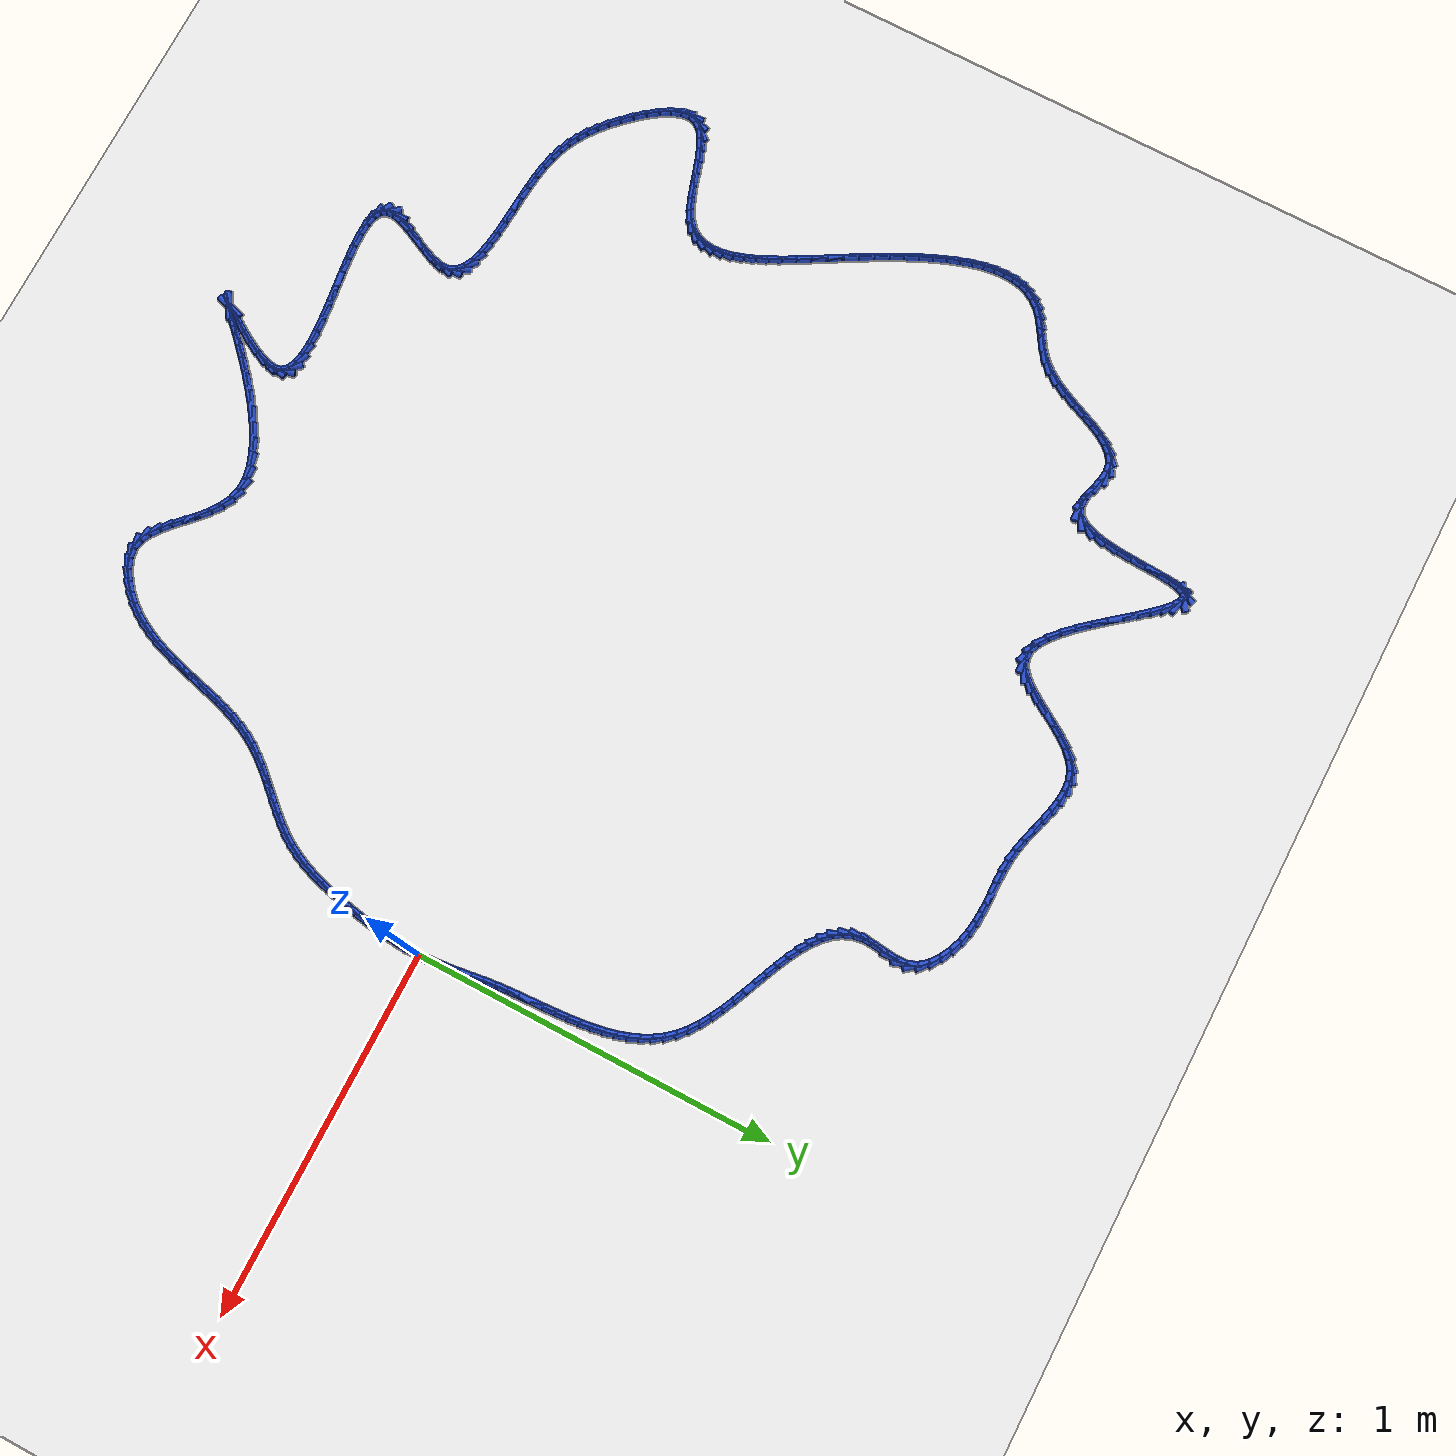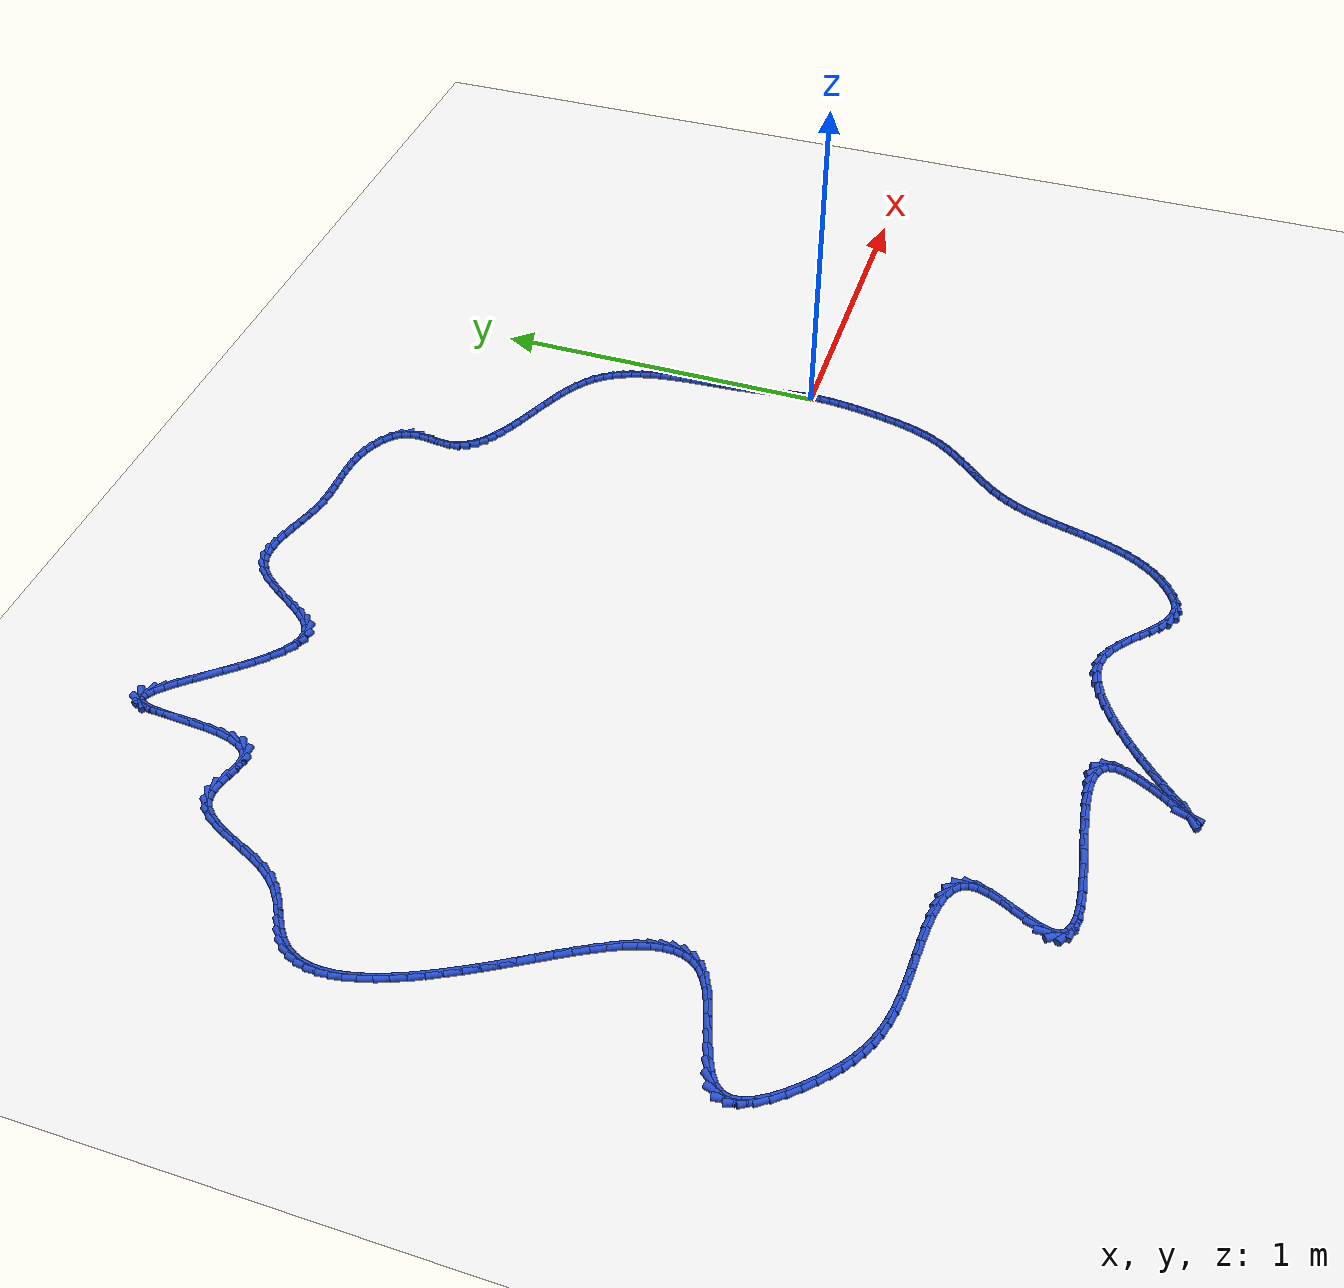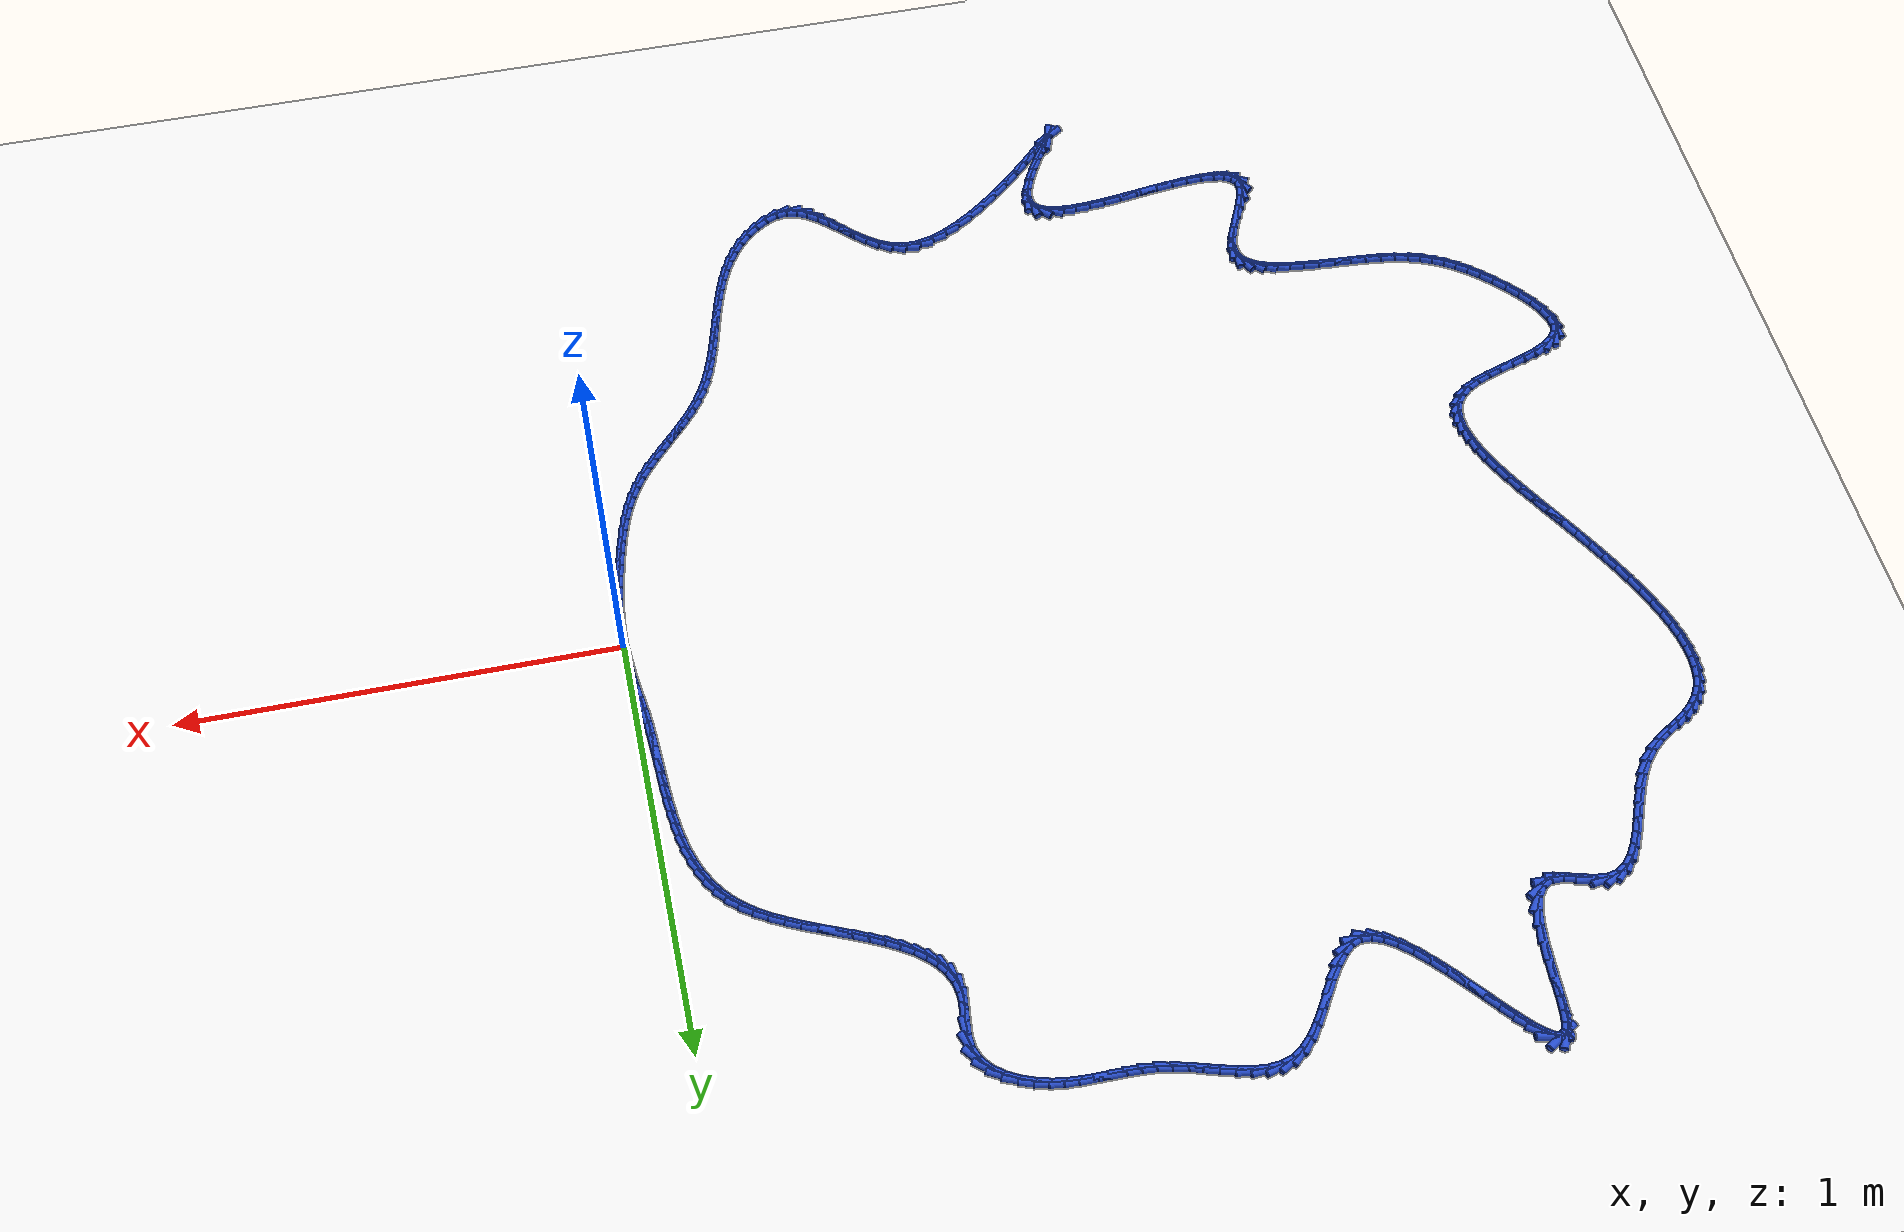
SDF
<sdf version="1.6">
 <world name="default">
  <light name="sun" type="directional">
   <pose>0 0 10 0 -0 0</pose>
   <diffuse>0.8 0.8 0.8 1</diffuse>
   <specular>0.2 0.2 0.2 1</specular>
   <attenuation>
    <range>1000</range>
    <constant>0.9</constant>
    <linear>0.01</linear>
    <quadratic>0.001</quadratic>
   </attenuation>
   <direction>-0.5 0.1 -0.9</direction>
  </light>
  <model name="ground_plane">
   <static>1</static>
   <link name="link">
    <collision name="collision">
     <geometry><plane><normal>0 0 1</normal><size>100 100</size></plane></geometry>
     <surface><friction><ode><mu>100</mu><mu2>50</mu2></ode></friction></surface>
    </collision>
    <visual name="visual">
     <cast_shadows>0</cast_shadows>
     <geometry><plane><normal>0 0 1</normal><size>100 100</size></plane></geometry>
     <material>
      <script><uri>file://media/materials/scripts/gazebo.material</uri><name>Gazebo/WhiteGlow</name></script>
     </material>
    </visual>
   </link>
  </model>
  <gravity>0 0 -9.8</gravity>
  <magnetic_field>6e-06 2.3e-05 -4.2e-05</magnetic_field>
  <atmosphere type="adiabatic"/>
  <physics name="default_physics" default="0" type="ode">
   <max_step_size>0.001</max_step_size>
   <real_time_factor>1</real_time_factor>
   <real_time_update_rate>1000</real_time_update_rate>
  </physics>
  <scene><ambient>0.4 0.4 0.4 1</ambient><background>0.7 0.7 0.7 1</background><shadows>1</shadows></scene>
  <spherical_coordinates>
   <surface_model>EARTH_WGS84</surface_model>
   <latitude_deg>0</latitude_deg>
   <longitude_deg>0</longitude_deg>
   <elevation>0</elevation>
   <heading_deg>0</heading_deg>
  </spherical_coordinates>
  <model name="line">
   <link name="link_0">
    <pose>-5.204170427930421e-18 -9.020562075079397e-17 0.01 0 1.57 -1.522232286232111</pose>
    <collision name="collision">
     <geometry><cylinder><radius>0.01</radius><length>0.08</length></cylinder></geometry>
    </collision>
    <visual name="visual">
     <material>
      <script><name>Gazebo/Blue</name><uri>file://media/materials/scripts/gazebo.material</uri></script>
     </material>
     <geometry><cylinder><radius>0.01</radius><length>0.08</length></cylinder></geometry>
    </visual>
   </link>
   <link name="link_1">
    <pose>-0.0014709635503436752 0.03026533512428548 0.01 0 1.57 -1.4829222144864138</pose>
    <collision name="collision">
     <geometry><cylinder><radius>0.01</radius><length>0.08</length></cylinder></geometry>
    </collision>
    <visual name="visual">
     <material>
      <script><name>Gazebo/Blue</name><uri>file://media/materials/scripts/gazebo.material</uri></script>
     </material>
     <geometry><cylinder><radius>0.01</radius><length>0.08</length></cylinder></geometry>
    </visual>
   </link>
   <link name="link_2">
    <pose>-0.0041331256183002926 0.060482496783488236 0.01 0 1.57 -1.4553366145338897</pose>
    <collision name="collision">
     <geometry><cylinder><radius>0.01</radius><length>0.08</length></cylinder></geometry>
    </collision>
    <visual name="visual">
     <material>
      <script><name>Gazebo/Blue</name><uri>file://media/materials/scripts/gazebo.material</uri></script>
     </material>
     <geometry><cylinder><radius>0.01</radius><length>0.08</length></cylinder></geometry>
    </visual>
   </link>
   <link name="link_3">
    <pose>-0.007645029595003838 0.0907639201038073 0.01 0 1.57 -1.4395641849911678</pose>
    <collision name="collision">
     <geometry><cylinder><radius>0.01</radius><length>0.08</length></cylinder></geometry>
    </collision>
    <visual name="visual">
     <material>
      <script><name>Gazebo/Blue</name><uri>file://media/materials/scripts/gazebo.material</uri></script>
     </material>
     <geometry><cylinder><radius>0.01</radius><length>0.08</length></cylinder></geometry>
    </visual>
   </link>
   <link name="link_4">
    <pose>-0.011665218871588296 0.12122204021144181 0.01 0 1.57 -1.4354534613786312</pose>
    <collision name="collision">
     <geometry><cylinder><radius>0.01</radius><length>0.08</length></cylinder></geometry>
    </collision>
    <visual name="visual">
     <material>
      <script><name>Gazebo/Blue</name><uri>file://media/materials/scripts/gazebo.material</uri></script>
     </material>
     <geometry><cylinder><radius>0.01</radius><length>0.08</length></cylinder></geometry>
    </visual>
   </link>
   <link name="link_5">
    <pose>-0.015852236839187652 0.1519692922325908 0.01 0 1.57 -1.4426882286479765</pose>
    <collision name="collision">
     <geometry><cylinder><radius>0.01</radius><length>0.08</length></cylinder></geometry>
    </collision>
    <visual name="visual">
     <material>
      <script><name>Gazebo/Blue</name><uri>file://media/materials/scripts/gazebo.material</uri></script>
     </material>
     <geometry><cylinder><radius>0.01</radius><length>0.08</length></cylinder></geometry>
    </visual>
   </link>
   <link name="link_6">
    <pose>-0.019864626888935883 0.18311811129345346 0.01 0 1.57 -1.4608188197446967</pose>
    <collision name="collision">
     <geometry><cylinder><radius>0.01</radius><length>0.08</length></cylinder></geometry>
    </collision>
    <visual name="visual">
     <material>
      <script><name>Gazebo/Blue</name><uri>file://media/materials/scripts/gazebo.material</uri></script>
     </material>
     <geometry><cylinder><radius>0.01</radius><length>0.08</length></cylinder></geometry>
    </visual>
   </link>
   <link name="link_7">
    <pose>-0.02336093241196698 0.21478093252022884 0.01 0 1.57 -1.4860278569934808</pose>
    <collision name="collision">
     <geometry><cylinder><radius>0.01</radius><length>0.08</length></cylinder></geometry>
    </collision>
    <visual name="visual">
     <material>
      <script><name>Gazebo/Blue</name><uri>file://media/materials/scripts/gazebo.material</uri></script>
     </material>
     <geometry><cylinder><radius>0.01</radius><length>0.08</length></cylinder></geometry>
    </visual>
   </link>
   <link name="link_8">
    <pose>-0.026100668854416493 0.24702371100806944 0.01 0 1.57 -1.5050241309093437</pose>
    <collision name="collision">
     <geometry><cylinder><radius>0.01</radius><length>0.08</length></cylinder></geometry>
    </collision>
    <visual name="visual">
     <material>
      <script><name>Gazebo/Blue</name><uri>file://media/materials/scripts/gazebo.material</uri></script>
     </material>
     <geometry><cylinder><radius>0.01</radius><length>0.08</length></cylinder></geometry>
    </visual>
   </link>
   <link name="link_9">
    <pose>-0.028254489105913917 0.279723144724126 0.01 0 1.57 -1.5149742220051203</pose>
    <collision name="collision">
     <geometry><cylinder><radius>0.01</radius><length>0.08</length></cylinder></geometry>
    </collision>
    <visual name="visual">
     <material>
      <script><name>Gazebo/Blue</name><uri>file://media/materials/scripts/gazebo.material</uri></script>
     </material>
     <geometry><cylinder><radius>0.01</radius><length>0.08</length></cylinder></geometry>
    </visual>
   </link>
   <link name="link_10">
    <pose>-0.0300976751328156 0.3127077681834478 0.01 0 1.57 -1.5162304851314876</pose>
    <collision name="collision">
     <geometry><cylinder><radius>0.01</radius><length>0.08</length></cylinder></geometry>
    </collision>
    <visual name="visual">
     <material>
      <script><name>Gazebo/Blue</name><uri>file://media/materials/scripts/gazebo.material</uri></script>
     </material>
     <geometry><cylinder><radius>0.01</radius><length>0.08</length></cylinder></geometry>
    </visual>
   </link>
   <link name="link_11">
    <pose>-0.031905508922908984 0.34580611589121907 0.01 0 1.57 -1.5088983215822322</pose>
    <collision name="collision">
     <geometry><cylinder><radius>0.01</radius><length>0.08</length></cylinder></geometry>
    </collision>
    <visual name="visual">
     <material>
      <script><name>Gazebo/Blue</name><uri>file://media/materials/scripts/gazebo.material</uri></script>
     </material>
     <geometry><cylinder><radius>0.01</radius><length>0.08</length></cylinder></geometry>
    </visual>
   </link>
   <link name="link_12">
    <pose>-0.03395327246398151 0.37884672235262384 0.01 0 1.57 -1.492842274083281</pose>
    <collision name="collision">
     <geometry><cylinder><radius>0.01</radius><length>0.08</length></cylinder></geometry>
    </collision>
    <visual name="visual">
     <material>
      <script><name>Gazebo/Blue</name><uri>file://media/materials/scripts/gazebo.material</uri></script>
     </material>
     <geometry><cylinder><radius>0.01</radius><length>0.08</length></cylinder></geometry>
    </visual>
   </link>
   <link name="link_13">
    <pose>-0.03651624774382062 0.411658122072846 0.01 0 1.57 -1.4676953295509052</pose>
    <collision name="collision">
     <geometry><cylinder><radius>0.01</radius><length>0.08</length></cylinder></geometry>
    </collision>
    <visual name="visual">
     <material>
      <script><name>Gazebo/Blue</name><uri>file://media/materials/scripts/gazebo.material</uri></script>
     </material>
     <geometry><cylinder><radius>0.01</radius><length>0.08</length></cylinder></geometry>
    </visual>
   </link>
   <link name="link_14">
    <pose>-0.03986971675021375 0.44406884955706993 0.01 0 1.57 -1.4328760174805222</pose>
    <collision name="collision">
     <geometry><cylinder><radius>0.01</radius><length>0.08</length></cylinder></geometry>
    </collision>
    <visual name="visual">
     <material>
      <script><name>Gazebo/Blue</name><uri>file://media/materials/scripts/gazebo.material</uri></script>
     </material>
     <geometry><cylinder><radius>0.01</radius><length>0.08</length></cylinder></geometry>
    </visual>
   </link>
   <link name="link_15">
    <pose>-0.04428896147094834 0.4759074393104796 0.01 0 1.57 -1.3876242073058669</pose>
    <collision name="collision">
     <geometry><cylinder><radius>0.01</radius><length>0.08</length></cylinder></geometry>
    </collision>
    <visual name="visual">
     <material>
      <script><name>Gazebo/Blue</name><uri>file://media/materials/scripts/gazebo.material</uri></script>
     </material>
     <geometry><cylinder><radius>0.01</radius><length>0.08</length></cylinder></geometry>
    </visual>
   </link>
   <link name="link_16">
    <pose>-0.05004926389381184 0.5070024258382588 0.01 0 1.57 -1.3310742017901627</pose>
    <collision name="collision">
     <geometry><cylinder><radius>0.01</radius><length>0.08</length></cylinder></geometry>
    </collision>
    <visual name="visual">
     <material>
      <script><name>Gazebo/Blue</name><uri>file://media/materials/scripts/gazebo.material</uri></script>
     </material>
     <geometry><cylinder><radius>0.01</radius><length>0.08</length></cylinder></geometry>
    </visual>
   </link>
   <link name="link_17">
    <pose>-0.057425906006591684 0.5371823436455921 0.01 0 1.57 -1.2623915712042322</pose>
    <collision name="collision">
     <geometry><cylinder><radius>0.01</radius><length>0.08</length></cylinder></geometry>
    </collision>
    <visual name="visual">
     <material>
      <script><name>Gazebo/Blue</name><uri>file://media/materials/scripts/gazebo.material</uri></script>
     </material>
     <geometry><cylinder><radius>0.01</radius><length>0.08</length></cylinder></geometry>
    </visual>
   </link>
   <link name="link_18">
    <pose>-0.06669416979707532 0.5662757272376634 0.01 0 1.57 -1.1810023733725474</pose>
    <collision name="collision">
     <geometry><cylinder><radius>0.01</radius><length>0.08</length></cylinder></geometry>
    </collision>
    <visual name="visual">
     <material>
      <script><name>Gazebo/Blue</name><uri>file://media/materials/scripts/gazebo.material</uri></script>
     </material>
     <geometry><cylinder><radius>0.01</radius><length>0.08</length></cylinder></geometry>
    </visual>
   </link>
   <link name="link_19">
    <pose>-0.07812933725305014 0.5941111111196565 0.01 0 1.57 -1.0869264948212116</pose>
    <collision name="collision">
     <geometry><cylinder><radius>0.01</radius><length>0.08</length></cylinder></geometry>
    </collision>
    <visual name="visual">
     <material>
      <script><name>Gazebo/Blue</name><uri>file://media/materials/scripts/gazebo.material</uri></script>
     </material>
     <geometry><cylinder><radius>0.01</radius><length>0.08</length></cylinder></geometry>
    </visual>
   </link>
   <link name="link_20">
    <pose>-0.09200669036230372 0.620517029796756 0.01 0 1.57 -0.9811721742202635</pose>
    <collision name="collision">
     <geometry><cylinder><radius>0.01</radius><length>0.08</length></cylinder></geometry>
    </collision>
    <visual name="visual">
     <material>
      <script><name>Gazebo/Blue</name><uri>file://media/materials/scripts/gazebo.material</uri></script>
     </material>
     <geometry><cylinder><radius>0.01</radius><length>0.08</length></cylinder></geometry>
    </visual>
   </link>
   <link name="link_21">
    <pose>-0.1086015111126234 0.6453220177741456 0.01 0 1.57 -0.8660536017765166</pose>
    <collision name="collision">
     <geometry><cylinder><radius>0.01</radius><length>0.08</length></cylinder></geometry>
    </collision>
    <visual name="visual">
     <material>
      <script><name>Gazebo/Blue</name><uri>file://media/materials/scripts/gazebo.material</uri></script>
     </material>
     <geometry><cylinder><radius>0.01</radius><length>0.08</length></cylinder></geometry>
    </visual>
   </link>
   <link name="link_22">
    <pose>-0.12818908149179659 0.6683546095570096 0.01 0 1.57 -0.7456979805366303</pose>
    <collision name="collision">
     <geometry><cylinder><radius>0.01</radius><length>0.08</length></cylinder></geometry>
    </collision>
    <visual name="visual">
     <material>
      <script><name>Gazebo/Blue</name><uri>file://media/materials/scripts/gazebo.material</uri></script>
     </material>
     <geometry><cylinder><radius>0.01</radius><length>0.08</length></cylinder></geometry>
    </visual>
   </link>
   <link name="link_23">
    <pose>-0.15103085002731698 0.6894511040095049 0.01 0 1.57 -0.636858438763827</pose>
    <collision name="collision">
     <geometry><cylinder><radius>0.01</radius><length>0.08</length></cylinder></geometry>
    </collision>
    <visual name="visual">
     <material>
      <script><name>Gazebo/Blue</name><uri>file://media/materials/scripts/gazebo.material</uri></script>
     </material>
     <geometry><cylinder><radius>0.01</radius><length>0.08</length></cylinder></geometry>
    </visual>
   </link>
   <link name="link_24">
    <pose>-0.1770045833075591 0.7086631506198284 0.01 0 1.57 -0.5527267282956707</pose>
    <collision name="collision">
     <geometry><cylinder><radius>0.01</radius><length>0.08</length></cylinder></geometry>
    </collision>
    <visual name="visual">
     <material>
      <script><name>Gazebo/Blue</name><uri>file://media/materials/scripts/gazebo.material</uri></script>
     </material>
     <geometry><cylinder><radius>0.01</radius><length>0.08</length></cylinder></geometry>
    </visual>
   </link>
   <link name="link_25">
    <pose>-0.20556400163948071 0.7262804049484294 0.01 0 1.57 -0.4903837553311104</pose>
    <collision name="collision">
     <geometry><cylinder><radius>0.01</radius><length>0.08</length></cylinder></geometry>
    </collision>
    <visual name="visual">
     <material>
      <script><name>Gazebo/Blue</name><uri>file://media/materials/scripts/gazebo.material</uri></script>
     </material>
     <geometry><cylinder><radius>0.01</radius><length>0.08</length></cylinder></geometry>
    </visual>
   </link>
   <link name="link_26">
    <pose>-0.23614089367152463 0.7426048322213057 0.01 0 1.57 -0.4465300705286888</pose>
    <collision name="collision">
     <geometry><cylinder><radius>0.01</radius><length>0.08</length></cylinder></geometry>
    </collision>
    <visual name="visual">
     <material>
      <script><name>Gazebo/Blue</name><uri>file://media/materials/scripts/gazebo.material</uri></script>
     </material>
     <geometry><cylinder><radius>0.01</radius><length>0.08</length></cylinder></geometry>
    </visual>
   </link>
   <link name="link_27">
    <pose>-0.26816704805213387 0.7579383976644556 0.01 0 1.57 -0.41871256408939855</pose>
    <collision name="collision">
     <geometry><cylinder><radius>0.01</radius><length>0.08</length></cylinder></geometry>
    </collision>
    <visual name="visual">
     <material>
      <script><name>Gazebo/Blue</name><uri>file://media/materials/scripts/gazebo.material</uri></script>
     </material>
     <geometry><cylinder><radius>0.01</radius><length>0.08</length></cylinder></geometry>
    </visual>
   </link>
   <link name="link_28">
    <pose>-0.3010742534297513 0.7725830665038765 0.01 0 1.57 -0.4054149249436557</pose>
    <collision name="collision">
     <geometry><cylinder><radius>0.01</radius><length>0.08</length></cylinder></geometry>
    </collision>
    <visual name="visual">
     <material>
      <script><name>Gazebo/Blue</name><uri>file://media/materials/scripts/gazebo.material</uri></script>
     </material>
     <geometry><cylinder><radius>0.01</radius><length>0.08</length></cylinder></geometry>
    </visual>
   </link>
   <link name="link_29">
    <pose>-0.33429429845282 0.7868408039655669 0.01 0 1.57 -0.40604587525706</pose>
    <collision name="collision">
     <geometry><cylinder><radius>0.01</radius><length>0.08</length></cylinder></geometry>
    </collision>
    <visual name="visual">
     <material>
      <script><name>Gazebo/Blue</name><uri>file://media/materials/scripts/gazebo.material</uri></script>
     </material>
     <geometry><cylinder><radius>0.01</radius><length>0.08</length></cylinder></geometry>
    </visual>
   </link>
   <link name="link_30">
    <pose>-0.36725897176978245 0.8010135752755241 0.01 0 1.57 -0.42094489326217294</pose>
    <collision name="collision">
     <geometry><cylinder><radius>0.01</radius><length>0.08</length></cylinder></geometry>
    </collision>
    <visual name="visual">
     <material>
      <script><name>Gazebo/Blue</name><uri>file://media/materials/scripts/gazebo.material</uri></script>
     </material>
     <geometry><cylinder><radius>0.01</radius><length>0.08</length></cylinder></geometry>
    </visual>
   </link>
   <link name="link_31">
    <pose>-0.39940006202908185 0.8154033456597461 0.01 0 1.57 -0.4514527013615953</pose>
    <collision name="collision">
     <geometry><cylinder><radius>0.01</radius><length>0.08</length></cylinder></geometry>
    </collision>
    <visual name="visual">
     <material>
      <script><name>Gazebo/Blue</name><uri>file://media/materials/scripts/gazebo.material</uri></script>
     </material>
     <geometry><cylinder><radius>0.01</radius><length>0.08</length></cylinder></geometry>
    </visual>
   </link>
   <link name="link_32">
    <pose>-0.4301493578791611 0.8303120803442311 0.01 0 1.57 -0.5000535907732365</pose>
    <collision name="collision">
     <geometry><cylinder><radius>0.01</radius><length>0.08</length></cylinder></geometry>
    </collision>
    <visual name="visual">
     <material>
      <script><name>Gazebo/Blue</name><uri>file://media/materials/scripts/gazebo.material</uri></script>
     </material>
     <geometry><cylinder><radius>0.01</radius><length>0.08</length></cylinder></geometry>
    </visual>
   </link>
   <link name="link_33">
    <pose>-0.4589386479684631 0.8460417445549768 0.01 0 1.57 -0.5705406208517386</pose>
    <collision name="collision">
     <geometry><cylinder><radius>0.01</radius><length>0.08</length></cylinder></geometry>
    </collision>
    <visual name="visual">
     <material>
      <script><name>Gazebo/Blue</name><uri>file://media/materials/scripts/gazebo.material</uri></script>
     </material>
     <geometry><cylinder><radius>0.01</radius><length>0.08</length></cylinder></geometry>
    </visual>
   </link>
   <link name="link_34">
    <pose>-0.4851997209454305 0.8628943035179809 0.01 0 1.57 -0.6680112293867284</pose>
    <collision name="collision">
     <geometry><cylinder><radius>0.01</radius><length>0.08</length></cylinder></geometry>
    </collision>
    <visual name="visual">
     <material>
      <script><name>Gazebo/Blue</name><uri>file://media/materials/scripts/gazebo.material</uri></script>
     </material>
     <geometry><cylinder><radius>0.01</radius><length>0.08</length></cylinder></geometry>
    </visual>
   </link>
   <link name="link_35">
    <pose>-0.5083643654585064 0.8811717224592412 0.01 0 1.57 -0.7981616529215781</pose>
    <collision name="collision">
     <geometry><cylinder><radius>0.01</radius><length>0.08</length></cylinder></geometry>
    </collision>
    <visual name="visual">
     <material>
      <script><name>Gazebo/Blue</name><uri>file://media/materials/scripts/gazebo.material</uri></script>
     </material>
     <geometry><cylinder><radius>0.01</radius><length>0.08</length></cylinder></geometry>
    </visual>
   </link>
   <link name="link_36">
    <pose>-0.5278643701561339 0.9011759666047564 0.01 0 1.57 -0.964837150017176</pose>
    <collision name="collision">
     <geometry><cylinder><radius>0.01</radius><length>0.08</length></cylinder></geometry>
    </collision>
    <visual name="visual">
     <material>
      <script><name>Gazebo/Blue</name><uri>file://media/materials/scripts/gazebo.material</uri></script>
     </material>
     <geometry><cylinder><radius>0.01</radius><length>0.08</length></cylinder></geometry>
    </visual>
   </link>
   <link name="link_37">
    <pose>-0.5431315236867555 0.9232090011805236 0.01 0 1.57 -1.165056455571028</pose>
    <collision name="collision">
     <geometry><cylinder><radius>0.01</radius><length>0.08</length></cylinder></geometry>
    </collision>
    <visual name="visual">
     <material>
      <script><name>Gazebo/Blue</name><uri>file://media/materials/scripts/gazebo.material</uri></script>
     </material>
     <geometry><cylinder><radius>0.01</radius><length>0.08</length></cylinder></geometry>
    </visual>
   </link>
   <link name="link_38">
    <pose>-0.5535976146988142 0.9475727914125407 0.01 0 1.57 -1.3841972647437364</pose>
    <collision name="collision">
     <geometry><cylinder><radius>0.01</radius><length>0.08</length></cylinder></geometry>
    </collision>
    <visual name="visual">
     <material>
      <script><name>Gazebo/Blue</name><uri>file://media/materials/scripts/gazebo.material</uri></script>
     </material>
     <geometry><cylinder><radius>0.01</radius><length>0.08</length></cylinder></geometry>
    </visual>
   </link>
   <link name="link_39">
    <pose>-0.5586944318407532 0.9745693025268061 0.01 0 1.57 1.5515692944739972</pose>
    <collision name="collision">
     <geometry><cylinder><radius>0.01</radius><length>0.08</length></cylinder></geometry>
    </collision>
    <visual name="visual">
     <material>
      <script><name>Gazebo/Blue</name><uri>file://media/materials/scripts/gazebo.material</uri></script>
     </material>
     <geometry><cylinder><radius>0.01</radius><length>0.08</length></cylinder></geometry>
    </visual>
   </link>
   <link name="link_40">
    <pose>-0.558121068033776 1.004386340444647 0.01 0 1.57 1.4497419668480511</pose>
    <collision name="collision">
     <geometry><cylinder><radius>0.01</radius><length>0.08</length></cylinder></geometry>
    </collision>
    <visual name="visual">
     <material>
      <script><name>Gazebo/Blue</name><uri>file://media/materials/scripts/gazebo.material</uri></script>
     </material>
     <geometry><cylinder><radius>0.01</radius><length>0.08</length></cylinder></geometry>
    </visual>
   </link>
   <link name="link_41">
    <pose>-0.5542677003114657 1.0360624129938558 0.01 0 1.57 1.4712720267406707</pose>
    <collision name="collision">
     <geometry><cylinder><radius>0.01</radius><length>0.08</length></cylinder></geometry>
    </collision>
    <visual name="visual">
     <material>
      <script><name>Gazebo/Blue</name><uri>file://media/materials/scripts/gazebo.material</uri></script>
     </material>
     <geometry><cylinder><radius>0.01</radius><length>0.08</length></cylinder></geometry>
    </visual>
   </link>
   <link name="link_42">
    <pose>-0.5510814858198664 1.067971078784661 0.01 0 1.57 -1.5233975627310024</pose>
    <collision name="collision">
     <geometry><cylinder><radius>0.01</radius><length>0.08</length></cylinder></geometry>
    </collision>
    <visual name="visual">
     <material>
      <script><name>Gazebo/Blue</name><uri>file://media/materials/scripts/gazebo.material</uri></script>
     </material>
     <geometry><cylinder><radius>0.01</radius><length>0.08</length></cylinder></geometry>
    </visual>
   </link>
   <link name="link_43">
    <pose>-0.5525285503235546 1.0984777953809441 0.01 0 1.57 -1.2261778521186517</pose>
    <collision name="collision">
     <geometry><cylinder><radius>0.01</radius><length>0.08</length></cylinder></geometry>
    </collision>
    <visual name="visual">
     <material>
      <script><name>Gazebo/Blue</name><uri>file://media/materials/scripts/gazebo.material</uri></script>
     </material>
     <geometry><cylinder><radius>0.01</radius><length>0.08</length></cylinder></geometry>
    </visual>
   </link>
   <link name="link_44">
    <pose>-0.562403459420681 1.1259889658442297 0.01 0 1.57 -0.8995294904261377</pose>
    <collision name="collision">
     <geometry><cylinder><radius>0.01</radius><length>0.08</length></cylinder></geometry>
    </collision>
    <visual name="visual">
     <material>
      <script><name>Gazebo/Blue</name><uri>file://media/materials/scripts/gazebo.material</uri></script>
     </material>
     <geometry><cylinder><radius>0.01</radius><length>0.08</length></cylinder></geometry>
    </visual>
   </link>
   <link name="link_45">
    <pose>-0.5812307617381497 1.14969143356187 0.01 0 1.57 -0.6622195922462348</pose>
    <collision name="collision">
     <geometry><cylinder><radius>0.01</radius><length>0.08</length></cylinder></geometry>
    </collision>
    <visual name="visual">
     <material>
      <script><name>Gazebo/Blue</name><uri>file://media/materials/scripts/gazebo.material</uri></script>
     </material>
     <geometry><cylinder><radius>0.01</radius><length>0.08</length></cylinder></geometry>
    </visual>
   </link>
   <link name="link_46">
    <pose>-0.6066014927486344 1.1694721703860071 0.01 0 1.57 -0.4923419884603313</pose>
    <collision name="collision">
     <geometry><cylinder><radius>0.01</radius><length>0.08</length></cylinder></geometry>
    </collision>
    <visual name="visual">
     <material>
      <script><name>Gazebo/Blue</name><uri>file://media/materials/scripts/gazebo.material</uri></script>
     </material>
     <geometry><cylinder><radius>0.01</radius><length>0.08</length></cylinder></geometry>
    </visual>
   </link>
   <link name="link_47">
    <pose>-0.6360026774160213 1.1852429718917425 0.01 0 1.57 -0.36097903088992506</pose>
    <collision name="collision">
     <geometry><cylinder><radius>0.01</radius><length>0.08</length></cylinder></geometry>
    </collision>
    <visual name="visual">
     <material>
      <script><name>Gazebo/Blue</name><uri>file://media/materials/scripts/gazebo.material</uri></script>
     </material>
     <geometry><cylinder><radius>0.01</radius><length>0.08</length></cylinder></geometry>
    </visual>
   </link>
   <link name="link_48">
    <pose>-0.6669270284989377 1.1969175639346736 0.01 0 1.57 -0.2473888436634144</pose>
    <collision name="collision">
     <geometry><cylinder><radius>0.01</radius><length>0.08</length></cylinder></geometry>
    </collision>
    <visual name="visual">
     <material>
      <script><name>Gazebo/Blue</name><uri>file://media/materials/scripts/gazebo.material</uri></script>
     </material>
     <geometry><cylinder><radius>0.01</radius><length>0.08</length></cylinder></geometry>
    </visual>
   </link>
   <link name="link_49">
    <pose>-0.6976697806847293 1.2046820261555424 0.01 0 1.57 -0.14951673683604147</pose>
    <collision name="collision">
     <geometry><cylinder><radius>0.01</radius><length>0.08</length></cylinder></geometry>
    </collision>
    <visual name="visual">
     <material>
      <script><name>Gazebo/Blue</name><uri>file://media/materials/scripts/gazebo.material</uri></script>
     </material>
     <geometry><cylinder><radius>0.01</radius><length>0.08</length></cylinder></geometry>
    </visual>
   </link>
   <link name="link_50">
    <pose>-0.7281503905147529 1.2092736542479174 0.01 0 1.57 -0.07314154999572284</pose>
    <collision name="collision">
     <geometry><cylinder><radius>0.01</radius><length>0.08</length></cylinder></geometry>
    </collision>
    <visual name="visual">
     <material>
      <script><name>Gazebo/Blue</name><uri>file://media/materials/scripts/gazebo.material</uri></script>
     </material>
     <geometry><cylinder><radius>0.01</radius><length>0.08</length></cylinder></geometry>
    </visual>
   </link>
   <link name="link_51">
    <pose>-0.7584844214644552 1.2114962971843248 0.01 0 1.57 -0.021694329339553755</pose>
    <collision name="collision">
     <geometry><cylinder><radius>0.01</radius><length>0.08</length></cylinder></geometry>
    </collision>
    <visual name="visual">
     <material>
      <script><name>Gazebo/Blue</name><uri>file://media/materials/scripts/gazebo.material</uri></script>
     </material>
     <geometry><cylinder><radius>0.01</radius><length>0.08</length></cylinder></geometry>
    </visual>
   </link>
   <link name="link_52">
    <pose>-0.7887874370092834 1.2121538039372923 0.01 0 1.57 0.0034152147165017427</pose>
    <collision name="collision">
     <geometry><cylinder><radius>0.01</radius><length>0.08</length></cylinder></geometry>
    </collision>
    <visual name="visual">
     <material>
      <script><name>Gazebo/Blue</name><uri>file://media/materials/scripts/gazebo.material</uri></script>
     </material>
     <geometry><cylinder><radius>0.01</radius><length>0.08</length></cylinder></geometry>
    </visual>
   </link>
   <link name="link_53">
    <pose>-0.8191750006246837 1.2120500234793463 0.01 0 1.57 0.0020014144347377232</pose>
    <collision name="collision">
     <geometry><cylinder><radius>0.01</radius><length>0.08</length></cylinder></geometry>
    </collision>
    <visual name="visual">
     <material>
      <script><name>Gazebo/Blue</name><uri>file://media/materials/scripts/gazebo.material</uri></script>
     </material>
     <geometry><cylinder><radius>0.01</radius><length>0.08</length></cylinder></geometry>
    </visual>
   </link>
   <link name="link_54">
    <pose>-0.8497626757861023 1.2119888047830127 0.01 0 1.57 -0.02540252542686296</pose>
    <collision name="collision">
     <geometry><cylinder><radius>0.01</radius><length>0.08</length></cylinder></geometry>
    </collision>
    <visual name="visual">
     <material>
      <script><name>Gazebo/Blue</name><uri>file://media/materials/scripts/gazebo.material</uri></script>
     </material>
     <geometry><cylinder><radius>0.01</radius><length>0.08</length></cylinder></geometry>
    </visual>
   </link>
   <link name="link_55">
    <pose>-0.8806660259689866 1.2127739968208193 0.01 0 1.57 -0.07756812306483099</pose>
    <collision name="collision">
     <geometry><cylinder><radius>0.01</radius><length>0.08</length></cylinder></geometry>
    </collision>
    <visual name="visual">
     <material>
      <script><name>Gazebo/Blue</name><uri>file://media/materials/scripts/gazebo.material</uri></script>
     </material>
     <geometry><cylinder><radius>0.01</radius><length>0.08</length></cylinder></geometry>
    </visual>
   </link>
   <link name="link_56">
    <pose>-0.9120006146487828 1.215209448565293 0.01 0 1.57 -0.1520966877153726</pose>
    <collision name="collision">
     <geometry><cylinder><radius>0.01</radius><length>0.08</length></cylinder></geometry>
    </collision>
    <visual name="visual">
     <material>
      <script><name>Gazebo/Blue</name><uri>file://media/materials/scripts/gazebo.material</uri></script>
     </material>
     <geometry><cylinder><radius>0.01</radius><length>0.08</length></cylinder></geometry>
    </visual>
   </link>
   <link name="link_57">
    <pose>-0.9438813751879057 1.220096146873792 0.01 0 1.57 -0.22882952763990239</pose>
    <collision name="collision">
     <geometry><cylinder><radius>0.01</radius><length>0.08</length></cylinder></geometry>
    </collision>
    <visual name="visual">
     <material>
      <script><name>Gazebo/Blue</name><uri>file://media/materials/scripts/gazebo.material</uri></script>
     </material>
     <geometry><cylinder><radius>0.01</radius><length>0.08</length></cylinder></geometry>
    </visual>
   </link>
   <link name="link_58">
    <pose>-0.9762933743034014 1.227645195080283 0.01 0 1.57 -0.27230655515974633</pose>
    <collision name="collision">
     <geometry><cylinder><radius>0.01</radius><length>0.08</length></cylinder></geometry>
    </collision>
    <visual name="visual">
     <material>
      <script><name>Gazebo/Blue</name><uri>file://media/materials/scripts/gazebo.material</uri></script>
     </material>
     <geometry><cylinder><radius>0.01</radius><length>0.08</length></cylinder></geometry>
    </visual>
   </link>
   <link name="link_59">
    <pose>-1.0089337336813127 1.2367597853999692 0.01 0 1.57 -0.28154102459989777</pose>
    <collision name="collision">
     <geometry><cylinder><radius>0.01</radius><length>0.08</length></cylinder></geometry>
    </collision>
    <visual name="visual">
     <material>
      <script><name>Gazebo/Blue</name><uri>file://media/materials/scripts/gazebo.material</uri></script>
     </material>
     <geometry><cylinder><radius>0.01</radius><length>0.08</length></cylinder></geometry>
    </visual>
   </link>
   <link name="link_60">
    <pose>-1.0414608923130513 1.2461674045453985 0.01 0 1.57 -0.25697464401926773</pose>
    <collision name="collision">
     <geometry><cylinder><radius>0.01</radius><length>0.08</length></cylinder></geometry>
    </collision>
    <visual name="visual">
     <material>
      <script><name>Gazebo/Blue</name><uri>file://media/materials/scripts/gazebo.material</uri></script>
     </material>
     <geometry><cylinder><radius>0.01</radius><length>0.08</length></cylinder></geometry>
    </visual>
   </link>
   <link name="link_61">
    <pose>-1.0735332891900293 1.2545955392291184 0.01 0 1.57 -0.19496324466805642</pose>
    <collision name="collision">
     <geometry><cylinder><radius>0.01</radius><length>0.08</length></cylinder></geometry>
    </collision>
    <visual name="visual">
     <material>
      <script><name>Gazebo/Blue</name><uri>file://media/materials/scripts/gazebo.material</uri></script>
     </material>
     <geometry><cylinder><radius>0.01</radius><length>0.08</length></cylinder></geometry>
    </visual>
   </link>
   <link name="link_62">
    <pose>-1.1048093633036586 1.2607716761636778 0.01 0 1.57 -0.08775628201706266</pose>
    <collision name="collision">
     <geometry><cylinder><radius>0.01</radius><length>0.08</length></cylinder></geometry>
    </collision>
    <visual name="visual">
     <material>
      <script><name>Gazebo/Blue</name><uri>file://media/materials/scripts/gazebo.material</uri></script>
     </material>
     <geometry><cylinder><radius>0.01</radius><length>0.08</length></cylinder></geometry>
    </visual>
   </link>
   <link name="link_63">
    <pose>-1.1349475536453517 1.2634233020616232 0.01 0 1.57 0.07472079359729969</pose>
    <collision name="collision">
     <geometry><cylinder><radius>0.01</radius><length>0.08</length></cylinder></geometry>
    </collision>
    <visual name="visual">
     <material>
      <script><name>Gazebo/Blue</name><uri>file://media/materials/scripts/gazebo.material</uri></script>
     </material>
     <geometry><cylinder><radius>0.01</radius><length>0.08</length></cylinder></geometry>
    </visual>
   </link>
   <link name="link_64">
    <pose>-1.1636062992065208 1.2612779036355042 0.01 0 1.57 0.29704041245757973</pose>
    <collision name="collision">
     <geometry><cylinder><radius>0.01</radius><length>0.08</length></cylinder></geometry>
    </collision>
    <visual name="visual">
     <material>
      <script><name>Gazebo/Blue</name><uri>file://media/materials/scripts/gazebo.material</uri></script>
     </material>
     <geometry><cylinder><radius>0.01</radius><length>0.08</length></cylinder></geometry>
    </visual>
   </link>
   <link name="link_65">
    <pose>-1.190444038978578 1.253062967597868 0.01 0 1.57 0.5567811980949366</pose>
    <collision name="collision">
     <geometry><cylinder><radius>0.01</radius><length>0.08</length></cylinder></geometry>
    </collision>
    <visual name="visual">
     <material>
      <script><name>Gazebo/Blue</name><uri>file://media/materials/scripts/gazebo.material</uri></script>
     </material>
     <geometry><cylinder><radius>0.01</radius><length>0.08</length></cylinder></geometry>
    </visual>
   </link>
   <link name="link_66">
    <pose>-1.2151617124431957 1.2376768449890503 0.01 0 1.57 0.765497317994727</pose>
    <collision name="collision">
     <geometry><cylinder><radius>0.01</radius><length>0.08</length></cylinder></geometry>
    </collision>
    <visual name="visual">
     <material>
      <script><name>Gazebo/Blue</name><uri>file://media/materials/scripts/gazebo.material</uri></script>
     </material>
     <geometry><cylinder><radius>0.01</radius><length>0.08</length></cylinder></geometry>
    </visual>
   </link>
   <link name="link_67">
    <pose>-1.237908082719474 1.2158182680757241 0.01 0 1.57 0.8972155700384897</pose>
    <collision name="collision">
     <geometry><cylinder><radius>0.01</radius><length>0.08</length></cylinder></geometry>
    </collision>
    <visual name="visual">
     <material>
      <script><name>Gazebo/Blue</name><uri>file://media/materials/scripts/gazebo.material</uri></script>
     </material>
     <geometry><cylinder><radius>0.01</radius><length>0.08</length></cylinder></geometry>
    </visual>
   </link>
   <link name="link_68">
    <pose>-1.2591002882071234 1.1892649157822357 0.01 0 1.57 0.9729503713252979</pose>
    <collision name="collision">
     <geometry><cylinder><radius>0.01</radius><length>0.08</length></cylinder></geometry>
    </collision>
    <visual name="visual">
     <material>
      <script><name>Gazebo/Blue</name><uri>file://media/materials/scripts/gazebo.material</uri></script>
     </material>
     <geometry><cylinder><radius>0.01</radius><length>0.08</length></cylinder></geometry>
    </visual>
   </link>
   <link name="link_69">
    <pose>-1.279159101670277 1.159809078234587 0.01 0 1.57 1.0065140315327161</pose>
    <collision name="collision">
     <geometry><cylinder><radius>0.01</radius><length>0.08</length></cylinder></geometry>
    </collision>
    <visual name="visual">
     <material>
      <script><name>Gazebo/Blue</name><uri>file://media/materials/scripts/gazebo.material</uri></script>
     </material>
     <geometry><cylinder><radius>0.01</radius><length>0.08</length></cylinder></geometry>
    </visual>
   </link>
   <link name="link_70">
    <pose>-1.2985052958730665 1.1292430455587805 0.01 0 1.57 1.0031792979952</pose>
    <collision name="collision">
     <geometry><cylinder><radius>0.01</radius><length>0.08</length></cylinder></geometry>
    </collision>
    <visual name="visual">
     <material>
      <script><name>Gazebo/Blue</name><uri>file://media/materials/scripts/gazebo.material</uri></script>
     </material>
     <geometry><cylinder><radius>0.01</radius><length>0.08</length></cylinder></geometry>
    </visual>
   </link>
   <link name="link_71">
    <pose>-1.317559643579624 1.0993591078808178 0.01 0 1.57 0.9601539322774792</pose>
    <collision name="collision">
     <geometry><cylinder><radius>0.01</radius><length>0.08</length></cylinder></geometry>
    </collision>
    <visual name="visual">
     <material>
      <script><name>Gazebo/Blue</name><uri>file://media/materials/scripts/gazebo.material</uri></script>
     </material>
     <geometry><cylinder><radius>0.01</radius><length>0.08</length></cylinder></geometry>
    </visual>
   </link>
   <link name="link_72">
    <pose>-1.3367429175540821 1.0719495553267013 0.01 0 1.57 0.8647608406528363</pose>
    <collision name="collision">
     <geometry><cylinder><radius>0.01</radius><length>0.08</length></cylinder></geometry>
    </collision>
    <visual name="visual">
     <material>
      <script><name>Gazebo/Blue</name><uri>file://media/materials/scripts/gazebo.material</uri></script>
     </material>
     <geometry><cylinder><radius>0.01</radius><length>0.08</length></cylinder></geometry>
    </visual>
   </link>
   <link name="link_73">
    <pose>-1.356475890560572 1.0488066780224325 0.01 0 1.57 0.6899026368323384</pose>
    <collision name="collision">
     <geometry><cylinder><radius>0.01</radius><length>0.08</length></cylinder></geometry>
    </collision>
    <visual name="visual">
     <material>
      <script><name>Gazebo/Blue</name><uri>file://media/materials/scripts/gazebo.material</uri></script>
     </material>
     <geometry><cylinder><radius>0.01</radius><length>0.08</length></cylinder></geometry>
    </visual>
   </link>
   <link name="link_74">
    <pose>-1.3771793353632267 1.0317227660940138 0.01 0 1.57 0.39581402573477303</pose>
    <collision name="collision">
     <geometry><cylinder><radius>0.01</radius><length>0.08</length></cylinder></geometry>
    </collision>
    <visual name="visual">
     <material>
      <script><name>Gazebo/Blue</name><uri>file://media/materials/scripts/gazebo.material</uri></script>
     </material>
     <geometry><cylinder><radius>0.01</radius><length>0.08</length></cylinder></geometry>
    </visual>
   </link>
   <link name="link_75">
    <pose>-1.3992740247261781 1.022490109667447 0.01 0 1.57 -0.009066226778642212</pose>
    <collision name="collision">
     <geometry><cylinder><radius>0.01</radius><length>0.08</length></cylinder></geometry>
    </collision>
    <visual name="visual">
     <material>
      <script><name>Gazebo/Blue</name><uri>file://media/materials/scripts/gazebo.material</uri></script>
     </material>
     <geometry><cylinder><radius>0.01</radius><length>0.08</length></cylinder></geometry>
    </visual>
   </link>
   <link name="link_76">
    <pose>-1.423132272507483 1.022706419879051 0.01 0 1.57 -0.3501738068152945</pose>
    <collision name="collision">
     <geometry><cylinder><radius>0.01</radius><length>0.08</length></cylinder></geometry>
    </collision>
    <visual name="visual">
     <material>
      <script><name>Gazebo/Blue</name><uri>file://media/materials/scripts/gazebo.material</uri></script>
     </material>
     <geometry><cylinder><radius>0.01</radius><length>0.08</length></cylinder></geometry>
    </visual>
   </link>
   <link name="link_77">
    <pose>-1.448641675409721 1.0320231036243914 0.01 0 1.57 -0.5644167396085268</pose>
    <collision name="collision">
     <geometry><cylinder><radius>0.01</radius><length>0.08</length></cylinder></geometry>
    </collision>
    <visual name="visual">
     <material>
      <script><name>Gazebo/Blue</name><uri>file://media/materials/scripts/gazebo.material</uri></script>
     </material>
     <geometry><cylinder><radius>0.01</radius><length>0.08</length></cylinder></geometry>
    </visual>
   </link>
   <link name="link_78">
    <pose>-1.4754107972388324 1.0489711558146522 0.01 0 1.57 -0.6962014273048526</pose>
    <collision name="collision">
     <geometry><cylinder><radius>0.01</radius><length>0.08</length></cylinder></geometry>
    </collision>
    <visual name="visual">
     <material>
      <script><name>Gazebo/Blue</name><uri>file://media/materials/scripts/gazebo.material</uri></script>
     </material>
     <geometry><cylinder><radius>0.01</radius><length>0.08</length></cylinder></geometry>
    </visual>
   </link>
   <link name="link_79">
    <pose>-1.5030448547760247 1.072068131918321 0.01 0 1.57 -0.7792989231242008</pose>
    <collision name="collision">
     <geometry><cylinder><radius>0.01</radius><length>0.08</length></cylinder></geometry>
    </collision>
    <visual name="visual">
     <material>
      <script><name>Gazebo/Blue</name><uri>file://media/materials/scripts/gazebo.material</uri></script>
     </material>
     <geometry><cylinder><radius>0.01</radius><length>0.08</length></cylinder></geometry>
    </visual>
   </link>
   <link name="link_80">
    <pose>-1.5311490648025043 1.0998315874038873 0.01 0 1.57 -0.8321769366018268</pose>
    <collision name="collision">
     <geometry><cylinder><radius>0.01</radius><length>0.08</length></cylinder></geometry>
    </collision>
    <visual name="visual">
     <material>
      <script><name>Gazebo/Blue</name><uri>file://media/materials/scripts/gazebo.material</uri></script>
     </material>
     <geometry><cylinder><radius>0.01</radius><length>0.08</length></cylinder></geometry>
    </visual>
   </link>
   <link name="link_81">
    <pose>-1.5593286440994776 1.1307790777398397 0.01 0 1.57 -0.8643770675902296</pose>
    <collision name="collision">
     <geometry><cylinder><radius>0.01</radius><length>0.08</length></cylinder></geometry>
    </collision>
    <visual name="visual">
     <material>
      <script><name>Gazebo/Blue</name><uri>file://media/materials/scripts/gazebo.material</uri></script>
     </material>
     <geometry><cylinder><radius>0.01</radius><length>0.08</length></cylinder></geometry>
    </visual>
   </link>
   <link name="link_82">
    <pose>-1.5871888094481519 1.1634281583946662 0.01 0 1.57 -0.8804591954986174</pose>
    <collision name="collision">
     <geometry><cylinder><radius>0.01</radius><length>0.08</length></cylinder></geometry>
    </collision>
    <visual name="visual">
     <material>
      <script><name>Gazebo/Blue</name><uri>file://media/materials/scripts/gazebo.material</uri></script>
     </material>
     <geometry><cylinder><radius>0.01</radius><length>0.08</length></cylinder></geometry>
    </visual>
   </link>
   <link name="link_83">
    <pose>-1.6143347776297345 1.1962963848368557 0.01 0 1.57 -0.8816947324710692</pose>
    <collision name="collision">
     <geometry><cylinder><radius>0.01</radius><length>0.08</length></cylinder></geometry>
    </collision>
    <visual name="visual">
     <material>
      <script><name>Gazebo/Blue</name><uri>file://media/materials/scripts/gazebo.material</uri></script>
     </material>
     <geometry><cylinder><radius>0.01</radius><length>0.08</length></cylinder></geometry>
    </visual>
   </link>
   <link name="link_84">
    <pose>-1.640371765425432 1.2279013125348976 0.01 0 1.57 -0.8662435763793179</pose>
    <collision name="collision">
     <geometry><cylinder><radius>0.01</radius><length>0.08</length></cylinder></geometry>
    </collision>
    <visual name="visual">
     <material>
      <script><name>Gazebo/Blue</name><uri>file://media/materials/scripts/gazebo.material</uri></script>
     </material>
     <geometry><cylinder><radius>0.01</radius><length>0.08</length></cylinder></geometry>
    </visual>
   </link>
   <link name="link_85">
    <pose>-1.6649049896164503 1.256760496957279 0.01 0 1.57 -0.8276092074091967</pose>
    <collision name="collision">
     <geometry><cylinder><radius>0.01</radius><length>0.08</length></cylinder></geometry>
    </collision>
    <visual name="visual">
     <material>
      <script><name>Gazebo/Blue</name><uri>file://media/materials/scripts/gazebo.material</uri></script>
     </material>
     <geometry><cylinder><radius>0.01</radius><length>0.08</length></cylinder></geometry>
    </visual>
   </link>
   <link name="link_86">
    <pose>-1.6875396669839973 1.28139149357249 0.01 0 1.57 -0.7492213634640081</pose>
    <collision name="collision">
     <geometry><cylinder><radius>0.01</radius><length>0.08</length></cylinder></geometry>
    </collision>
    <visual name="visual">
     <material>
      <script><name>Gazebo/Blue</name><uri>file://media/materials/scripts/gazebo.material</uri></script>
     </material>
     <geometry><cylinder><radius>0.01</radius><length>0.08</length></cylinder></geometry>
    </visual>
   </link>
   <link name="link_87">
    <pose>-1.7078810143092795 1.300311857849019 0.01 0 1.57 -0.5863719423166787</pose>
    <collision name="collision">
     <geometry><cylinder><radius>0.01</radius><length>0.08</length></cylinder></geometry>
    </collision>
    <visual name="visual">
     <material>
      <script><name>Gazebo/Blue</name><uri>file://media/materials/scripts/gazebo.material</uri></script>
     </material>
     <geometry><cylinder><radius>0.01</radius><length>0.08</length></cylinder></geometry>
    </visual>
   </link>
   <link name="link_88">
    <pose>-1.7255342483735046 1.3120391452553544 0.01 0 1.57 -0.2064659449492439</pose>
    <collision name="collision">
     <geometry><cylinder><radius>0.01</radius><length>0.08</length></cylinder></geometry>
    </collision>
    <visual name="visual">
     <material>
      <script><name>Gazebo/Blue</name><uri>file://media/materials/scripts/gazebo.material</uri></script>
     </material>
     <geometry><cylinder><radius>0.01</radius><length>0.08</length></cylinder></geometry>
    </visual>
   </link>
   <link name="link_89">
    <pose>-1.740104585957878 1.315090911259985 0.01 0 1.57 0.5694984922600155</pose>
    <collision name="collision">
     <geometry><cylinder><radius>0.01</radius><length>0.08</length></cylinder></geometry>
    </collision>
    <visual name="visual">
     <material>
      <script><name>Gazebo/Blue</name><uri>file://media/materials/scripts/gazebo.material</uri></script>
     </material>
     <geometry><cylinder><radius>0.01</radius><length>0.08</length></cylinder></geometry>
    </visual>
   </link>
   <link name="link_90">
    <pose>-1.7511984208587388 1.3079879588643313 0.01 0 1.57 1.1680947320906683</pose>
    <collision name="collision">
     <geometry><cylinder><radius>0.01</radius><length>0.08</length></cylinder></geometry>
    </collision>
    <visual name="visual">
     <material>
      <script><name>Gazebo/Blue</name><uri>file://media/materials/scripts/gazebo.material</uri></script>
     </material>
     <geometry><cylinder><radius>0.01</radius><length>0.08</length></cylinder></geometry>
    </visual>
   </link>
   <link name="link_91">
    <pose>-1.7587705209930389 1.2902122991285345 0.01 0 1.57 1.3913517327843767</pose>
    <collision name="collision">
     <geometry><cylinder><radius>0.01</radius><length>0.08</length></cylinder></geometry>
    </collision>
    <visual name="visual">
     <material>
      <script><name>Gazebo/Blue</name><uri>file://media/materials/scripts/gazebo.material</uri></script>
     </material>
     <geometry><cylinder><radius>0.01</radius><length>0.08</length></cylinder></geometry>
    </visual>
   </link>
   <link name="link_92">
    <pose>-1.763608208018566 1.26354306370137 0.01 0 1.57 1.4809774849759714</pose>
    <collision name="collision">
     <geometry><cylinder><radius>0.01</radius><length>0.08</length></cylinder></geometry>
    </collision>
    <visual name="visual">
     <material>
      <script><name>Gazebo/Blue</name><uri>file://media/materials/scripts/gazebo.material</uri></script>
     </material>
     <geometry><cylinder><radius>0.01</radius><length>0.08</length></cylinder></geometry>
    </visual>
   </link>
   <link name="link_93">
    <pose>-1.7666205520707914 1.2300953036095459 0.01 0 1.57 1.5158529048032474</pose>
    <collision name="collision">
     <geometry><cylinder><radius>0.01</radius><length>0.08</length></cylinder></geometry>
    </collision>
    <visual name="visual">
     <material>
      <script><name>Gazebo/Blue</name><uri>file://media/materials/scripts/gazebo.material</uri></script>
     </material>
     <geometry><cylinder><radius>0.01</radius><length>0.08</length></cylinder></geometry>
    </visual>
   </link>
   <link name="link_94">
    <pose>-1.7687166232851848 1.1919840698797715 0.01 0 1.57 1.5194669781931232</pose>
    <collision name="collision">
     <geometry><cylinder><radius>0.01</radius><length>0.08</length></cylinder></geometry>
    </collision>
    <visual name="visual">
     <material>
      <script><name>Gazebo/Blue</name><uri>file://media/materials/scripts/gazebo.material</uri></script>
     </material>
     <geometry><cylinder><radius>0.01</radius><length>0.08</length></cylinder></geometry>
    </visual>
   </link>
   <link name="link_95">
    <pose>-1.770805491797217 1.1513244135387555 0.01 0 1.57 1.498144777492259</pose>
    <collision name="collision">
     <geometry><cylinder><radius>0.01</radius><length>0.08</length></cylinder></geometry>
    </collision>
    <visual name="visual">
     <material>
      <script><name>Gazebo/Blue</name><uri>file://media/materials/scripts/gazebo.material</uri></script>
     </material>
     <geometry><cylinder><radius>0.01</radius><length>0.08</length></cylinder></geometry>
    </visual>
   </link>
   <link name="link_96">
    <pose>-1.7737962277423578 1.1102313856132073 0.01 0 1.57 1.449559047472858</pose>
    <collision name="collision">
     <geometry><cylinder><radius>0.01</radius><length>0.08</length></cylinder></geometry>
    </collision>
    <visual name="visual">
     <material>
      <script><name>Gazebo/Blue</name><uri>file://media/materials/scripts/gazebo.material</uri></script>
     </material>
     <geometry><cylinder><radius>0.01</radius><length>0.08</length></cylinder></geometry>
    </visual>
   </link>
   <link name="link_97">
    <pose>-1.7785979012560782 1.0708200371298355 0.01 0 1.57 1.3626584848872938</pose>
    <collision name="collision">
     <geometry><cylinder><radius>0.01</radius><length>0.08</length></cylinder></geometry>
    </collision>
    <visual name="visual">
     <material>
      <script><name>Gazebo/Blue</name><uri>file://media/materials/scripts/gazebo.material</uri></script>
     </material>
     <geometry><cylinder><radius>0.01</radius><length>0.08</length></cylinder></geometry>
    </visual>
   </link>
   <link name="link_98">
    <pose>-1.7861195824738485 1.0352054191153492 0.01 0 1.57 1.211665745398329</pose>
    <collision name="collision">
     <geometry><cylinder><radius>0.01</radius><length>0.08</length></cylinder></geometry>
    </collision>
    <visual name="visual">
     <material>
      <script><name>Gazebo/Blue</name><uri>file://media/materials/scripts/gazebo.material</uri></script>
     </material>
     <geometry><cylinder><radius>0.01</radius><length>0.08</length></cylinder></geometry>
    </visual>
   </link>
   <link name="link_99">
    <pose>-1.7972703415311393 1.0055025825964574 0.01 0 1.57 0.944280736452537</pose>
    <collision name="collision">
     <geometry><cylinder><radius>0.01</radius><length>0.08</length></cylinder></geometry>
    </collision>
    <visual name="visual">
     <material>
      <script><name>Gazebo/Blue</name><uri>file://media/materials/scripts/gazebo.material</uri></script>
     </material>
     <geometry><cylinder><radius>0.01</radius><length>0.08</length></cylinder></geometry>
    </visual>
   </link>
   <link name="link_100">
    <pose>-1.8129592485634203 0.983826578599869 0.01 0 1.57 0.4995408670516688</pose>
    <collision name="collision">
     <geometry><cylinder><radius>0.01</radius><length>0.08</length></cylinder></geometry>
    </collision>
    <visual name="visual">
     <material>
      <script><name>Gazebo/Blue</name><uri>file://media/materials/scripts/gazebo.material</uri></script>
     </material>
     <geometry><cylinder><radius>0.01</radius><length>0.08</length></cylinder></geometry>
    </visual>
   </link>
   <link name="link_101">
    <pose>-1.8340953737061618 0.9722924581522927 0.01 0 1.57 0.0031661683400550887</pose>
    <collision name="collision">
     <geometry><cylinder><radius>0.01</radius><length>0.08</length></cylinder></geometry>
    </collision>
    <visual name="visual">
     <material>
      <script><name>Gazebo/Blue</name><uri>file://media/materials/scripts/gazebo.material</uri></script>
     </material>
     <geometry><cylinder><radius>0.01</radius><length>0.08</length></cylinder></geometry>
    </visual>
   </link>
   <link name="link_102">
    <pose>-1.8612000784919709 0.9722066398073677 0.01 0 1.57 -0.23364873128672217</pose>
    <collision name="collision">
     <geometry><cylinder><radius>0.01</radius><length>0.08</length></cylinder></geometry>
    </collision>
    <visual name="visual">
     <material>
      <script><name>Gazebo/Blue</name><uri>file://media/materials/scripts/gazebo.material</uri></script>
     </material>
     <geometry><cylinder><radius>0.01</radius><length>0.08</length></cylinder></geometry>
    </visual>
   </link>
   <link name="link_103">
    <pose>-1.8922653135903613 0.9796000239937267 0.01 0 1.57 -0.2679857738535311</pose>
    <collision name="collision">
     <geometry><cylinder><radius>0.01</radius><length>0.08</length></cylinder></geometry>
    </collision>
    <visual name="visual">
     <material>
      <script><name>Gazebo/Blue</name><uri>file://media/materials/scripts/gazebo.material</uri></script>
     </material>
     <geometry><cylinder><radius>0.01</radius><length>0.08</length></cylinder></geometry>
    </visual>
   </link>
   <link name="link_104">
    <pose>-1.9242686487217995 0.9883878465161001 0.01 0 1.57 -0.13612090513714556</pose>
    <collision name="collision">
     <geometry><cylinder><radius>0.01</radius><length>0.08</length></cylinder></geometry>
    </collision>
    <visual name="visual">
     <material>
      <script><name>Gazebo/Blue</name><uri>file://media/materials/scripts/gazebo.material</uri></script>
     </material>
     <geometry><cylinder><radius>0.01</radius><length>0.08</length></cylinder></geometry>
    </visual>
   </link>
   <link name="link_105">
    <pose>-1.9541880637186182 0.9924858461632704 0.01 0 1.57 0.1804391101125435</pose>
    <collision name="collision">
     <geometry><cylinder><radius>0.01</radius><length>0.08</length></cylinder></geometry>
    </collision>
    <visual name="visual">
     <material>
      <script><name>Gazebo/Blue</name><uri>file://media/materials/scripts/gazebo.material</uri></script>
     </material>
     <geometry><cylinder><radius>0.01</radius><length>0.08</length></cylinder></geometry>
    </visual>
   </link>
   <link name="link_106">
    <pose>-1.9799987664048868 0.9877773747811328 0.01 0 1.57 0.5272306696854829</pose>
    <collision name="collision">
     <geometry><cylinder><radius>0.01</radius><length>0.08</length></cylinder></geometry>
    </collision>
    <visual name="visual">
     <material>
      <script><name>Gazebo/Blue</name><uri>file://media/materials/scripts/gazebo.material</uri></script>
     </material>
     <geometry><cylinder><radius>0.01</radius><length>0.08</length></cylinder></geometry>
    </visual>
   </link>
   <link name="link_107">
    <pose>-2.002092707090293 0.9749142164194387 0.01 0 1.57 0.7990552548292474</pose>
    <collision name="collision">
     <geometry><cylinder><radius>0.01</radius><length>0.08</length></cylinder></geometry>
    </collision>
    <visual name="visual">
     <material>
      <script><name>Gazebo/Blue</name><uri>file://media/materials/scripts/gazebo.material</uri></script>
     </material>
     <geometry><cylinder><radius>0.01</radius><length>0.08</length></cylinder></geometry>
    </visual>
   </link>
   <link name="link_108">
    <pose>-2.021220789057481 0.955256398942121 0.01 0 1.57 0.9777116052703662</pose>
    <collision name="collision">
     <geometry><cylinder><radius>0.01</radius><length>0.08</length></cylinder></geometry>
    </collision>
    <visual name="visual">
     <material>
      <script><name>Gazebo/Blue</name><uri>file://media/materials/scripts/gazebo.material</uri></script>
     </material>
     <geometry><cylinder><radius>0.01</radius><length>0.08</length></cylinder></geometry>
    </visual>
   </link>
   <link name="link_109">
    <pose>-2.0381339155890936 0.9301639502131106 0.01 0 1.57 1.0836910795722672</pose>
    <collision name="collision">
     <geometry><cylinder><radius>0.01</radius><length>0.08</length></cylinder></geometry>
    </collision>
    <visual name="visual">
     <material>
      <script><name>Gazebo/Blue</name><uri>file://media/materials/scripts/gazebo.material</uri></script>
     </material>
     <geometry><cylinder><radius>0.01</radius><length>0.08</length></cylinder></geometry>
    </visual>
   </link>
   <link name="link_110">
    <pose>-2.053582989967775 0.9009968980963404 0.01 0 1.57 1.137837191953618</pose>
    <collision name="collision">
     <geometry><cylinder><radius>0.01</radius><length>0.08</length></cylinder></geometry>
    </collision>
    <visual name="visual">
     <material>
      <script><name>Gazebo/Blue</name><uri>file://media/materials/scripts/gazebo.material</uri></script>
     </material>
     <geometry><cylinder><radius>0.01</radius><length>0.08</length></cylinder></geometry>
    </visual>
   </link>
   <link name="link_111">
    <pose>-2.068318915476167 0.8691152704557418 0.01 0 1.57 1.1525205816904691</pose>
    <collision name="collision">
     <geometry><cylinder><radius>0.01</radius><length>0.08</length></cylinder></geometry>
    </collision>
    <visual name="visual">
     <material>
      <script><name>Gazebo/Blue</name><uri>file://media/materials/scripts/gazebo.material</uri></script>
     </material>
     <geometry><cylinder><radius>0.01</radius><length>0.08</length></cylinder></geometry>
    </visual>
   </link>
   <link name="link_112">
    <pose>-2.0830925953969137 0.8358790951552474 0.01 0 1.57 1.132818817298513</pose>
    <collision name="collision">
     <geometry><cylinder><radius>0.01</radius><length>0.08</length></cylinder></geometry>
    </collision>
    <visual name="visual">
     <material>
      <script><name>Gazebo/Blue</name><uri>file://media/materials/scripts/gazebo.material</uri></script>
     </material>
     <geometry><cylinder><radius>0.01</radius><length>0.08</length></cylinder></geometry>
    </visual>
   </link>
   <link name="link_113">
    <pose>-2.098654933012657 0.8026484000587881 0.01 0 1.57 1.0782251467264803</pose>
    <collision name="collision">
     <geometry><cylinder><radius>0.01</radius><length>0.08</length></cylinder></geometry>
    </collision>
    <visual name="visual">
     <material>
      <script><name>Gazebo/Blue</name><uri>file://media/materials/scripts/gazebo.material</uri></script>
     </material>
     <geometry><cylinder><radius>0.01</radius><length>0.08</length></cylinder></geometry>
    </visual>
   </link>
   <link name="link_114">
    <pose>-2.115756831606041 0.7707832130302966 0.01 0 1.57 0.9836036331536047</pose>
    <collision name="collision">
     <geometry><cylinder><radius>0.01</radius><length>0.08</length></cylinder></geometry>
    </collision>
    <visual name="visual">
     <material>
      <script><name>Gazebo/Blue</name><uri>file://media/materials/scripts/gazebo.material</uri></script>
     </material>
     <geometry><cylinder><radius>0.01</radius><length>0.08</length></cylinder></geometry>
    </visual>
   </link>
   <link name="link_115">
    <pose>-2.13514919445971 0.7416435619337048 0.01 0 1.57 0.8414688541394961</pose>
    <collision name="collision">
     <geometry><cylinder><radius>0.01</radius><length>0.08</length></cylinder></geometry>
    </collision>
    <visual name="visual">
     <material>
      <script><name>Gazebo/Blue</name><uri>file://media/materials/scripts/gazebo.material</uri></script>
     </material>
     <geometry><cylinder><radius>0.01</radius><length>0.08</length></cylinder></geometry>
    </visual>
   </link>
   <link name="link_116">
    <pose>-2.157562295279019 0.7165647633417827 0.01 0 1.57 0.689191156214235</pose>
    <collision name="collision">
     <geometry><cylinder><radius>0.01</radius><length>0.08</length></cylinder></geometry>
    </collision>
    <visual name="visual">
     <material>
      <script><name>Gazebo/Blue</name><uri>file://media/materials/scripts/gazebo.material</uri></script>
     </material>
     <geometry><cylinder><radius>0.01</radius><length>0.08</length></cylinder></geometry>
    </visual>
   </link>
   <link name="link_117">
    <pose>-2.1827985362832583 0.695770676130698 0.01 0 1.57 0.5907189803474093</pose>
    <collision name="collision">
     <geometry><cylinder><radius>0.01</radius><length>0.08</length></cylinder></geometry>
    </collision>
    <visual name="visual">
     <material>
      <script><name>Gazebo/Blue</name><uri>file://media/materials/scripts/gazebo.material</uri></script>
     </material>
     <geometry><cylinder><radius>0.01</radius><length>0.08</length></cylinder></geometry>
    </visual>
   </link>
   <link name="link_118">
    <pose>-2.2093766258451506 0.6779474770436091 0.01 0 1.57 0.5534953499788212</pose>
    <collision name="collision">
     <geometry><cylinder><radius>0.01</radius><length>0.08</length></cylinder></geometry>
    </collision>
    <visual name="visual">
     <material>
      <script><name>Gazebo/Blue</name><uri>file://media/materials/scripts/gazebo.material</uri></script>
     </material>
     <geometry><cylinder><radius>0.01</radius><length>0.08</length></cylinder></geometry>
    </visual>
   </link>
   <link name="link_119">
    <pose>-2.235721119360957 0.6616685609870554 0.01 0 1.57 0.5824593974868777</pose>
    <collision name="collision">
     <geometry><cylinder><radius>0.01</radius><length>0.08</length></cylinder></geometry>
    </collision>
    <visual name="visual">
     <material>
      <script><name>Gazebo/Blue</name><uri>file://media/materials/scripts/gazebo.material</uri></script>
     </material>
     <geometry><cylinder><radius>0.01</radius><length>0.08</length></cylinder></geometry>
    </visual>
   </link>
   <link name="link_120">
    <pose>-2.260256572226936 0.6455073228675753 0.01 0 1.57 0.689918790912646</pose>
    <collision name="collision">
     <geometry><cylinder><radius>0.01</radius><length>0.08</length></cylinder></geometry>
    </collision>
    <visual name="visual">
     <material>
      <script><name>Gazebo/Blue</name><uri>file://media/materials/scripts/gazebo.material</uri></script>
     </material>
     <geometry><cylinder><radius>0.01</radius><length>0.08</length></cylinder></geometry>
    </visual>
   </link>
   <link name="link_121">
    <pose>-2.281417248377929 0.6280455416397124 0.01 0 1.57 0.8604591923142747</pose>
    <collision name="collision">
     <geometry><cylinder><radius>0.01</radius><length>0.08</length></cylinder></geometry>
    </collision>
    <visual name="visual">
     <material>
      <script><name>Gazebo/Blue</name><uri>file://media/materials/scripts/gazebo.material</uri></script>
     </material>
     <geometry><cylinder><radius>0.01</radius><length>0.08</length></cylinder></geometry>
    </visual>
   </link>
   <link name="link_122">
    <pose>-2.298290065239091 0.6084286112807847 0.01 0 1.57 1.040726236391041</pose>
    <collision name="collision">
     <geometry><cylinder><radius>0.01</radius><length>0.08</length></cylinder></geometry>
    </collision>
    <visual name="visual">
     <material>
      <script><name>Gazebo/Blue</name><uri>file://media/materials/scripts/gazebo.material</uri></script>
     </material>
     <geometry><cylinder><radius>0.01</radius><length>0.08</length></cylinder></geometry>
    </visual>
   </link>
   <link name="link_123">
    <pose>-2.3110160886672038 0.5867122616524928 0.01 0 1.57 1.2143545795935167</pose>
    <collision name="collision">
     <geometry><cylinder><radius>0.01</radius><length>0.08</length></cylinder></geometry>
    </collision>
    <visual name="visual">
     <material>
      <script><name>Gazebo/Blue</name><uri>file://media/materials/scripts/gazebo.material</uri></script>
     </material>
     <geometry><cylinder><radius>0.01</radius><length>0.08</length></cylinder></geometry>
    </visual>
   </link>
   <link name="link_124">
    <pose>-2.3198322243008063 0.5630349874244772 0.01 0 1.57 1.3717718442089943</pose>
    <collision name="collision">
     <geometry><cylinder><radius>0.01</radius><length>0.08</length></cylinder></geometry>
    </collision>
    <visual name="visual">
     <material>
      <script><name>Gazebo/Blue</name><uri>file://media/materials/scripts/gazebo.material</uri></script>
     </material>
     <geometry><cylinder><radius>0.01</radius><length>0.08</length></cylinder></geometry>
    </visual>
   </link>
   <link name="link_125">
    <pose>-2.324975377778438 0.5375352832663773 0.01 0 1.57 1.5080807268448222</pose>
    <collision name="collision">
     <geometry><cylinder><radius>0.01</radius><length>0.08</length></cylinder></geometry>
    </collision>
    <visual name="visual">
     <material>
      <script><name>Gazebo/Blue</name><uri>file://media/materials/scripts/gazebo.material</uri></script>
     </material>
     <geometry><cylinder><radius>0.01</radius><length>0.08</length></cylinder></geometry>
    </visual>
   </link>
   <link name="link_126">
    <pose>-2.3266824547386364 0.5103516438478338 0.01 0 1.57 -1.518906239013687</pose>
    <collision name="collision">
     <geometry><cylinder><radius>0.01</radius><length>0.08</length></cylinder></geometry>
    </collision>
    <visual name="visual">
     <material>
      <script><name>Gazebo/Blue</name><uri>file://media/materials/scripts/gazebo.material</uri></script>
     </material>
     <geometry><cylinder><radius>0.01</radius><length>0.08</length></cylinder></geometry>
    </visual>
   </link>
   <link name="link_127">
    <pose>-2.3251903608199407 0.4816225638384867 0.01 0 1.57 -1.4240503943725096</pose>
    <collision name="collision">
     <geometry><cylinder><radius>0.01</radius><length>0.08</length></cylinder></geometry>
    </collision>
    <visual name="visual">
     <material>
      <script><name>Gazebo/Blue</name><uri>file://media/materials/scripts/gazebo.material</uri></script>
     </material>
     <geometry><cylinder><radius>0.01</radius><length>0.08</length></cylinder></geometry>
    </visual>
   </link>
   <link name="link_128">
    <pose>-2.3207360016608893 0.45148653790797616 0.01 0 1.57 -1.346038176333954</pose>
    <collision name="collision">
     <geometry><cylinder><radius>0.01</radius><length>0.08</length></cylinder></geometry>
    </collision>
    <visual name="visual">
     <material>
      <script><name>Gazebo/Blue</name><uri>file://media/materials/scripts/gazebo.material</uri></script>
     </material>
     <geometry><cylinder><radius>0.01</radius><length>0.08</length></cylinder></geometry>
    </visual>
   </link>
   <link name="link_129">
    <pose>-2.3135562829000214 0.42008206072594234 0.01 0 1.57 -1.2819402800190427</pose>
    <collision name="collision">
     <geometry><cylinder><radius>0.01</radius><length>0.08</length></cylinder></geometry>
    </collision>
    <visual name="visual">
     <material>
      <script><name>Gazebo/Blue</name><uri>file://media/materials/scripts/gazebo.material</uri></script>
     </material>
     <geometry><cylinder><radius>0.01</radius><length>0.08</length></cylinder></geometry>
    </visual>
   </link>
   <link name="link_130">
    <pose>-2.3038881101758735 0.3875476269620254 0.01 0 1.57 -1.2291966558021017</pose>
    <collision name="collision">
     <geometry><cylinder><radius>0.01</radius><length>0.08</length></cylinder></geometry>
    </collision>
    <visual name="visual">
     <material>
      <script><name>Gazebo/Blue</name><uri>file://media/materials/scripts/gazebo.material</uri></script>
     </material>
     <geometry><cylinder><radius>0.01</radius><length>0.08</length></cylinder></geometry>
    </visual>
   </link>
   <link name="link_131">
    <pose>-2.291968389126987 0.3540217312858655 0.01 0 1.57 -1.18571409596821</pose>
    <collision name="collision">
     <geometry><cylinder><radius>0.01</radius><length>0.08</length></cylinder></geometry>
    </collision>
    <visual name="visual">
     <material>
      <script><name>Gazebo/Blue</name><uri>file://media/materials/scripts/gazebo.material</uri></script>
     </material>
     <geometry><cylinder><radius>0.01</radius><length>0.08</length></cylinder></geometry>
    </visual>
   </link>
   <link name="link_132">
    <pose>-2.278034025391899 0.31964286836710293 0.01 0 1.57 -1.1498373942153215</pose>
    <collision name="collision">
     <geometry><cylinder><radius>0.01</radius><length>0.08</length></cylinder></geometry>
    </collision>
    <visual name="visual">
     <material>
      <script><name>Gazebo/Blue</name><uri>file://media/materials/scripts/gazebo.material</uri></script>
     </material>
     <geometry><cylinder><radius>0.01</radius><length>0.08</length></cylinder></geometry>
    </visual>
   </link>
   <link name="link_133">
    <pose>-2.2623219246091484 0.28454953287537815 0.01 0 1.57 -1.1202806927299558</pose>
    <collision name="collision">
     <geometry><cylinder><radius>0.01</radius><length>0.08</length></cylinder></geometry>
    </collision>
    <visual name="visual">
     <material>
      <script><name>Gazebo/Blue</name><uri>file://media/materials/scripts/gazebo.material</uri></script>
     </material>
     <geometry><cylinder><radius>0.01</radius><length>0.08</length></cylinder></geometry>
    </visual>
   </link>
   <link name="link_134">
    <pose>-2.2450689924172735 0.24888021948033046 0.01 0 1.57 -1.096056143245267</pose>
    <collision name="collision">
     <geometry><cylinder><radius>0.01</radius><length>0.08</length></cylinder></geometry>
    </collision>
    <visual name="visual">
     <material>
      <script><name>Gazebo/Blue</name><uri>file://media/materials/scripts/gazebo.material</uri></script>
     </material>
     <geometry><cylinder><radius>0.01</radius><length>0.08</length></cylinder></geometry>
    </visual>
   </link>
   <link name="link_135">
    <pose>-2.2265121344548127 0.21277342285160028 0.01 0 1.57 -1.0764129334075316</pose>
    <collision name="collision">
     <geometry><cylinder><radius>0.01</radius><length>0.08</length></cylinder></geometry>
    </collision>
    <visual name="visual">
     <material>
      <script><name>Gazebo/Blue</name><uri>file://media/materials/scripts/gazebo.material</uri></script>
     </material>
     <geometry><cylinder><radius>0.01</radius><length>0.08</length></cylinder></geometry>
    </visual>
   </link>
   <link name="link_136">
    <pose>-2.2068882563603056 0.17636763765882812 0.01 0 1.57 -1.060789542800911</pose>
    <collision name="collision">
     <geometry><cylinder><radius>0.01</radius><length>0.08</length></cylinder></geometry>
    </collision>
    <visual name="visual">
     <material>
      <script><name>Gazebo/Blue</name><uri>file://media/materials/scripts/gazebo.material</uri></script>
     </material>
     <geometry><cylinder><radius>0.01</radius><length>0.08</length></cylinder></geometry>
    </visual>
   </link>
   <link name="link_137">
    <pose>-2.186434263772289 0.1398013585716538 0.01 0 1.57 -1.0491652100260271</pose>
    <collision name="collision">
     <geometry><cylinder><radius>0.01</radius><length>0.08</length></cylinder></geometry>
    </collision>
    <visual name="visual">
     <material>
      <script><name>Gazebo/Blue</name><uri>file://media/materials/scripts/gazebo.material</uri></script>
     </material>
     <geometry><cylinder><radius>0.01</radius><length>0.08</length></cylinder></geometry>
    </visual>
   </link>
   <link name="link_138">
    <pose>-2.165408357883322 0.10321736792099218 0.01 0 1.57 -1.0440502867330452</pose>
    <collision name="collision">
     <geometry><cylinder><radius>0.01</radius><length>0.08</length></cylinder></geometry>
    </collision>
    <visual name="visual">
     <material>
      <script><name>Gazebo/Blue</name><uri>file://media/materials/scripts/gazebo.material</uri></script>
     </material>
     <geometry><cylinder><radius>0.01</radius><length>0.08</length></cylinder></geometry>
    </visual>
   </link>
   <link name="link_139">
    <pose>-2.144223656436363 0.06678963904097732 0.01 0 1.57 -1.0465957655842741</pose>
    <collision name="collision">
     <geometry><cylinder><radius>0.01</radius><length>0.08</length></cylinder></geometry>
    </collision>
    <visual name="visual">
     <material>
      <script><name>Gazebo/Blue</name><uri>file://media/materials/scripts/gazebo.material</uri></script>
     </material>
     <geometry><cylinder><radius>0.01</radius><length>0.08</length></cylinder></geometry>
    </visual>
   </link>
   <link name="link_140">
    <pose>-2.123361756008121 0.03070593284052731 0.01 0 1.57 -1.0571411717745225</pose>
    <collision name="collision">
     <geometry><cylinder><radius>0.01</radius><length>0.08</length></cylinder></geometry>
    </collision>
    <visual name="visual">
     <material>
      <script><name>Gazebo/Blue</name><uri>file://media/materials/scripts/gazebo.material</uri></script>
     </material>
     <geometry><cylinder><radius>0.01</radius><length>0.08</length></cylinder></geometry>
    </visual>
   </link>
   <link name="link_141">
    <pose>-2.103304556238174 -0.004845928752557706 0.01 0 1.57 -1.0765255783290721</pose>
    <collision name="collision">
     <geometry><cylinder><radius>0.01</radius><length>0.08</length></cylinder></geometry>
    </collision>
    <visual name="visual">
     <material>
      <script><name>Gazebo/Blue</name><uri>file://media/materials/scripts/gazebo.material</uri></script>
     </material>
     <geometry><cylinder><radius>0.01</radius><length>0.08</length></cylinder></geometry>
    </visual>
   </link>
   <link name="link_142">
    <pose>-2.0845339567660983 -0.039678123810475974 0.01 0 1.57 -1.106211875910068</pose>
    <collision name="collision">
     <geometry><cylinder><radius>0.01</radius><length>0.08</length></cylinder></geometry>
    </collision>
    <visual name="visual">
     <material>
      <script><name>Gazebo/Blue</name><uri>file://media/materials/scripts/gazebo.material</uri></script>
     </material>
     <geometry><cylinder><radius>0.01</radius><length>0.08</length></cylinder></geometry>
    </visual>
   </link>
   <link name="link_143">
    <pose>-2.0675318572314736 -0.0736028304054263 0.01 0 1.57 -1.1484878683057174</pose>
    <collision name="collision">
     <geometry><cylinder><radius>0.01</radius><length>0.08</length></cylinder></geometry>
    </collision>
    <visual name="visual">
     <material>
      <script><name>Gazebo/Blue</name><uri>file://media/materials/scripts/gazebo.material</uri></script>
     </material>
     <geometry><cylinder><radius>0.01</radius><length>0.08</length></cylinder></geometry>
    </visual>
   </link>
   <link name="link_144">
    <pose>-2.0527801572738786 -0.10643222660960742 0.01 0 1.57 -1.2067681965961092</pose>
    <collision name="collision">
     <geometry><cylinder><radius>0.01</radius><length>0.08</length></cylinder></geometry>
    </collision>
    <visual name="visual">
     <material>
      <script><name>Gazebo/Blue</name><uri>file://media/materials/scripts/gazebo.material</uri></script>
     </material>
     <geometry><cylinder><radius>0.01</radius><length>0.08</length></cylinder></geometry>
    </visual>
   </link>
   <link name="link_145">
    <pose>-2.0407607565328894 -0.1379784904952182 0.01 0 1.57 -1.2859840495448682</pose>
    <collision name="collision">
     <geometry><cylinder><radius>0.01</radius><length>0.08</length></cylinder></geometry>
    </collision>
    <visual name="visual">
     <material>
      <script><name>Gazebo/Blue</name><uri>file://media/materials/scripts/gazebo.material</uri></script>
     </material>
     <geometry><cylinder><radius>0.01</radius><length>0.08</length></cylinder></geometry>
    </visual>
   </link>
   <link name="link_146">
    <pose>-2.0319555546480856 -0.1680538001344574 0.01 0 1.57 -1.3929035726428316</pose>
    <collision name="collision">
     <geometry><cylinder><radius>0.01</radius><length>0.08</length></cylinder></geometry>
    </collision>
    <visual name="visual">
     <material>
      <script><name>Gazebo/Blue</name><uri>file://media/materials/scripts/gazebo.material</uri></script>
     </material>
     <geometry><cylinder><radius>0.01</radius><length>0.08</length></cylinder></geometry>
    </visual>
   </link>
   <link name="link_147">
    <pose>-2.0268464512590443 -0.19647033359952368 0.01 0 1.57 -1.53576709645639</pose>
    <collision name="collision">
     <geometry><cylinder><radius>0.01</radius><length>0.08</length></cylinder></geometry>
    </collision>
    <visual name="visual">
     <material>
      <script><name>Gazebo/Blue</name><uri>file://media/materials/scripts/gazebo.material</uri></script>
     </material>
     <geometry><cylinder><radius>0.01</radius><length>0.08</length></cylinder></geometry>
    </visual>
   </link>
   <link name="link_148">
    <pose>-2.0259153460053447 -0.22304026896261608 0.01 0 1.57 1.4199750988048945</pose>
    <collision name="collision">
     <geometry><cylinder><radius>0.01</radius><length>0.08</length></cylinder></geometry>
    </collision>
    <visual name="visual">
     <material>
      <script><name>Gazebo/Blue</name><uri>file://media/materials/scripts/gazebo.material</uri></script>
     </material>
     <geometry><cylinder><radius>0.01</radius><length>0.08</length></cylinder></geometry>
    </visual>
   </link>
   <link name="link_149">
    <pose>-2.029644138526563 -0.24757578429593308 0.01 0 1.57 1.1924058096728491</pose>
    <collision name="collision">
     <geometry><cylinder><radius>0.01</radius><length>0.08</length></cylinder></geometry>
    </collision>
    <visual name="visual">
     <material>
      <script><name>Gazebo/Blue</name><uri>file://media/materials/scripts/gazebo.material</uri></script>
     </material>
     <geometry><cylinder><radius>0.01</radius><length>0.08</length></cylinder></geometry>
    </visual>
   </link>
   <link name="link_150">
    <pose>-2.038514728462279 -0.2698890576716738 0.01 0 1.57 0.941368545891448</pose>
    <collision name="collision">
     <geometry><cylinder><radius>0.01</radius><length>0.08</length></cylinder></geometry>
    </collision>
    <visual name="visual">
     <material>
      <script><name>Gazebo/Blue</name><uri>file://media/materials/scripts/gazebo.material</uri></script>
     </material>
     <geometry><cylinder><radius>0.01</radius><length>0.08</length></cylinder></geometry>
    </visual>
   </link>
   <link name="link_151">
    <pose>-2.0530090154520706 -0.28979226716203677 0.01 0 1.57 0.6987867918585061</pose>
    <collision name="collision">
     <geometry><cylinder><radius>0.01</radius><length>0.08</length></cylinder></geometry>
    </collision>
    <visual name="visual">
     <material>
      <script><name>Gazebo/Blue</name><uri>file://media/materials/scripts/gazebo.material</uri></script>
     </material>
     <geometry><cylinder><radius>0.01</radius><length>0.08</length></cylinder></geometry>
    </visual>
   </link>
   <link name="link_152">
    <pose>-2.073606441094195 -0.30709856565579424 0.01 0 1.57 0.5069188649373703</pose>
    <collision name="collision">
     <geometry><cylinder><radius>0.01</radius><length>0.08</length></cylinder></geometry>
    </collision>
    <visual name="visual">
     <material>
      <script><name>Gazebo/Blue</name><uri>file://media/materials/scripts/gazebo.material</uri></script>
     </material>
     <geometry><cylinder><radius>0.01</radius><length>0.08</length></cylinder></geometry>
    </visual>
   </link>
   <link name="link_153">
    <pose>-2.1001865183673067 -0.3218590273317002 0.01 0 1.57 0.391218545048139</pose>
    <collision name="collision">
     <geometry><cylinder><radius>0.01</radius><length>0.08</length></cylinder></geometry>
    </collision>
    <visual name="visual">
     <material>
      <script><name>Gazebo/Blue</name><uri>file://media/materials/scripts/gazebo.material</uri></script>
     </material>
     <geometry><cylinder><radius>0.01</radius><length>0.08</length></cylinder></geometry>
    </visual>
   </link>
   <link name="link_154">
    <pose>-2.1312492886156287 -0.3346718009037579 0.01 0 1.57 0.32853390056385845</pose>
    <collision name="collision">
     <geometry><cylinder><radius>0.01</radius><length>0.08</length></cylinder></geometry>
    </collision>
    <visual name="visual">
     <material>
      <script><name>Gazebo/Blue</name><uri>file://media/materials/scripts/gazebo.material</uri></script>
     </material>
     <geometry><cylinder><radius>0.01</radius><length>0.08</length></cylinder></geometry>
    </visual>
   </link>
   <link name="link_155">
    <pose>-2.165101625347015 -0.3462116421010546 0.01 0 1.57 0.30341061377185236</pose>
    <collision name="collision">
     <geometry><cylinder><radius>0.01</radius><length>0.08</length></cylinder></geometry>
    </collision>
    <visual name="visual">
     <material>
      <script><name>Gazebo/Blue</name><uri>file://media/materials/scripts/gazebo.material</uri></script>
     </material>
     <geometry><cylinder><radius>0.01</radius><length>0.08</length></cylinder></geometry>
    </visual>
   </link>
   <link name="link_156">
    <pose>-2.2000504020693255 -0.35715330665267736 0.01 0 1.57 0.31037813354107574</pose>
    <collision name="collision">
     <geometry><cylinder><radius>0.01</radius><length>0.08</length></cylinder></geometry>
    </collision>
    <visual name="visual">
     <material>
      <script><name>Gazebo/Blue</name><uri>file://media/materials/scripts/gazebo.material</uri></script>
     </material>
     <geometry><cylinder><radius>0.01</radius><length>0.08</length></cylinder></geometry>
    </visual>
   </link>
   <link name="link_157">
    <pose>-2.2344024922904158 -0.36817155028771315 0.01 0 1.57 0.3518134291060292</pose>
    <collision name="collision">
     <geometry><cylinder><radius>0.01</radius><length>0.08</length></cylinder></geometry>
    </collision>
    <visual name="visual">
     <material>
      <script><name>Gazebo/Blue</name><uri>file://media/materials/scripts/gazebo.material</uri></script>
     </material>
     <geometry><cylinder><radius>0.01</radius><length>0.08</length></cylinder></geometry>
    </visual>
   </link>
   <link name="link_158">
    <pose>-2.2664647695181412 -0.37994112873524905 0.01 0 1.57 0.43931363850416283</pose>
    <collision name="collision">
     <geometry><cylinder><radius>0.01</radius><length>0.08</length></cylinder></geometry>
    </collision>
    <visual name="visual">
     <material>
      <script><name>Gazebo/Blue</name><uri>file://media/materials/scripts/gazebo.material</uri></script>
     </material>
     <geometry><cylinder><radius>0.01</radius><length>0.08</length></cylinder></geometry>
    </visual>
   </link>
   <link name="link_159">
    <pose>-2.2945441072603607 -0.3931367977243721 0.01 0 1.57 0.5990754714090254</pose>
    <collision name="collision">
     <geometry><cylinder><radius>0.01</radius><length>0.08</length></cylinder></geometry>
    </collision>
    <visual name="visual">
     <material>
      <script><name>Gazebo/Blue</name><uri>file://media/materials/scripts/gazebo.material</uri></script>
     </material>
     <geometry><cylinder><radius>0.01</radius><length>0.08</length></cylinder></geometry>
    </visual>
   </link>
   <link name="link_160">
    <pose>-2.3169473790249304 -0.40843331298416935 0.01 0 1.57 0.8769083112500563</pose>
    <collision name="collision">
     <geometry><cylinder><radius>0.01</radius><length>0.08</length></cylinder></geometry>
    </collision>
    <visual name="visual">
     <material>
      <script><name>Gazebo/Blue</name><uri>file://media/materials/scripts/gazebo.material</uri></script>
     </material>
     <geometry><cylinder><radius>0.01</radius><length>0.08</length></cylinder></geometry>
    </visual>
   </link>
   <link name="link_161">
    <pose>-2.3319814583197065 -0.4265054302437279 0.01 0 1.57 1.2956327655114852</pose>
    <collision name="collision">
     <geometry><cylinder><radius>0.01</radius><length>0.08</length></cylinder></geometry>
    </collision>
    <visual name="visual">
     <material>
      <script><name>Gazebo/Blue</name><uri>file://media/materials/scripts/gazebo.material</uri></script>
     </material>
     <geometry><cylinder><radius>0.01</radius><length>0.08</length></cylinder></geometry>
    </visual>
   </link>
   <link name="link_162">
    <pose>-2.338044595430633 -0.4479811504073528 0.01 0 1.57 -1.4547996952405402</pose>
    <collision name="collision">
     <geometry><cylinder><radius>0.01</radius><length>0.08</length></cylinder></geometry>
    </collision>
    <visual name="visual">
     <material>
      <script><name>Gazebo/Blue</name><uri>file://media/materials/scripts/gazebo.material</uri></script>
     </material>
     <geometry><cylinder><radius>0.01</radius><length>0.08</length></cylinder></geometry>
    </visual>
   </link>
   <link name="link_163">
    <pose>-2.3351699633232914 -0.47265193226198954 0.01 0 1.57 -1.2033547015904633</pose>
    <collision name="collision">
     <geometry><cylinder><radius>0.01</radius><length>0.08</length></cylinder></geometry>
    </collision>
    <visual name="visual">
     <material>
      <script><name>Gazebo/Blue</name><uri>file://media/materials/scripts/gazebo.material</uri></script>
     </material>
     <geometry><cylinder><radius>0.01</radius><length>0.08</length></cylinder></geometry>
    </visual>
   </link>
   <link name="link_164">
    <pose>-2.3248019880547433 -0.49958713766365026 0.01 0 1.57 -1.0455227967140226</pose>
    <collision name="collision">
     <geometry><cylinder><radius>0.01</radius><length>0.08</length></cylinder></geometry>
    </collision>
    <visual name="visual">
     <material>
      <script><name>Gazebo/Blue</name><uri>file://media/materials/scripts/gazebo.material</uri></script>
     </material>
     <geometry><cylinder><radius>0.01</radius><length>0.08</length></cylinder></geometry>
    </visual>
   </link>
   <link name="link_165">
    <pose>-2.3084314348136714 -0.5278324180900142 0.01 0 1.57 -0.9401357561276776</pose>
    <collision name="collision">
     <geometry><cylinder><radius>0.01</radius><length>0.08</length></cylinder></geometry>
    </collision>
    <visual name="visual">
     <material>
      <script><name>Gazebo/Blue</name><uri>file://media/materials/scripts/gazebo.material</uri></script>
     </material>
     <geometry><cylinder><radius>0.01</radius><length>0.08</length></cylinder></geometry>
    </visual>
   </link>
   <link name="link_166">
    <pose>-2.287549068788756 -0.5564334250187599 0.01 0 1.57 -0.864204048610214</pose>
    <collision name="collision">
     <geometry><cylinder><radius>0.01</radius><length>0.08</length></cylinder></geometry>
    </collision>
    <visual name="visual">
     <material>
      <script><name>Gazebo/Blue</name><uri>file://media/materials/scripts/gazebo.material</uri></script>
     </material>
     <geometry><cylinder><radius>0.01</radius><length>0.08</length></cylinder></geometry>
    </visual>
   </link>
   <link name="link_167">
    <pose>-2.263645655168677 -0.5844358099275665 0.01 0 1.57 -0.8049727147378422</pose>
    <collision name="collision">
     <geometry><cylinder><radius>0.01</radius><length>0.08</length></cylinder></geometry>
    </collision>
    <visual name="visual">
     <material>
      <script><name>Gazebo/Blue</name><uri>file://media/materials/scripts/gazebo.material</uri></script>
     </material>
     <geometry><cylinder><radius>0.01</radius><length>0.08</length></cylinder></geometry>
    </visual>
   </link>
   <link name="link_168">
    <pose>-2.2382119591421166 -0.6108852242941125 0.01 0 1.57 -0.754148735744835</pose>
    <collision name="collision">
     <geometry><cylinder><radius>0.01</radius><length>0.08</length></cylinder></geometry>
    </collision>
    <visual name="visual">
     <material>
      <script><name>Gazebo/Blue</name><uri>file://media/materials/scripts/gazebo.material</uri></script>
     </material>
     <geometry><cylinder><radius>0.01</radius><length>0.08</length></cylinder></geometry>
    </visual>
   </link>
   <link name="link_169">
    <pose>-2.2127025938659477 -0.6348481067182372 0.01 0 1.57 -0.6993967250432398</pose>
    <collision name="collision">
     <geometry><cylinder><radius>0.01</radius><length>0.08</length></cylinder></geometry>
    </collision>
    <visual name="visual">
     <material>
      <script><name>Gazebo/Blue</name><uri>file://media/materials/scripts/gazebo.material</uri></script>
     </material>
     <geometry><cylinder><radius>0.01</radius><length>0.08</length></cylinder></geometry>
    </visual>
   </link>
   <link name="link_170">
    <pose>-2.1876599718949836 -0.655915403673977 0.01 0 1.57 -0.6323896616276623</pose>
    <collision name="collision">
     <geometry><cylinder><radius>0.01</radius><length>0.08</length></cylinder></geometry>
    </collision>
    <visual name="visual">
     <material>
      <script><name>Gazebo/Blue</name><uri>file://media/materials/scripts/gazebo.material</uri></script>
     </material>
     <geometry><cylinder><radius>0.01</radius><length>0.08</length></cylinder></geometry>
    </visual>
   </link>
   <link name="link_171">
    <pose>-2.1626670808503974 -0.6742297231133936 0.01 0 1.57 -0.5543867806039049</pose>
    <collision name="collision">
     <geometry><cylinder><radius>0.01</radius><length>0.08</length></cylinder></geometry>
    </collision>
    <visual name="visual">
     <material>
      <script><name>Gazebo/Blue</name><uri>file://media/materials/scripts/gazebo.material</uri></script>
     </material>
     <geometry><cylinder><radius>0.01</radius><length>0.08</length></cylinder></geometry>
    </visual>
   </link>
   <link name="link_172">
    <pose>-2.1372613039115826 -0.6899598951690197 0.01 0 1.57 -0.4689366251350924</pose>
    <collision name="collision">
     <geometry><cylinder><radius>0.01</radius><length>0.08</length></cylinder></geometry>
    </collision>
    <visual name="visual">
     <material>
      <script><name>Gazebo/Blue</name><uri>file://media/materials/scripts/gazebo.material</uri></script>
     </material>
     <geometry><cylinder><radius>0.01</radius><length>0.08</length></cylinder></geometry>
    </visual>
   </link>
   <link name="link_173">
    <pose>-2.110980024257932 -0.7032747499733875 0.01 0 1.57 -0.3811494379396673</pose>
    <collision name="collision">
     <geometry><cylinder><radius>0.01</radius><length>0.08</length></cylinder></geometry>
    </collision>
    <visual name="visual">
     <material>
      <script><name>Gazebo/Blue</name><uri>file://media/materials/scripts/gazebo.material</uri></script>
     </material>
     <geometry><cylinder><radius>0.01</radius><length>0.08</length></cylinder></geometry>
    </visual>
   </link>
   <link name="link_174">
    <pose>-2.0833606250688397 -0.7143431176590296 0.01 0 1.57 -0.29658388620212495</pose>
    <collision name="collision">
     <geometry><cylinder><radius>0.01</radius><length>0.08</length></cylinder></geometry>
    </collision>
    <visual name="visual">
     <material>
      <script><name>Gazebo/Blue</name><uri>file://media/materials/scripts/gazebo.material</uri></script>
     </material>
     <geometry><cylinder><radius>0.01</radius><length>0.08</length></cylinder></geometry>
    </visual>
   </link>
   <link name="link_175">
    <pose>-2.0539404895236983 -0.7233338283584788 0.01 0 1.57 -0.2199050241682146</pose>
    <collision name="collision">
     <geometry><cylinder><radius>0.01</radius><length>0.08</length></cylinder></geometry>
    </collision>
    <visual name="visual">
     <material>
      <script><name>Gazebo/Blue</name><uri>file://media/materials/scripts/gazebo.material</uri></script>
     </material>
     <geometry><cylinder><radius>0.01</radius><length>0.08</length></cylinder></geometry>
    </visual>
   </link>
   <link name="link_176">
    <pose>-2.0222570008019005 -0.7304157122042672 0.01 0 1.57 -0.15402208383314334</pose>
    <collision name="collision">
     <geometry><cylinder><radius>0.01</radius><length>0.08</length></cylinder></geometry>
    </collision>
    <visual name="visual">
     <material>
      <script><name>Gazebo/Blue</name><uri>file://media/materials/scripts/gazebo.material</uri></script>
     </material>
     <geometry><cylinder><radius>0.01</radius><length>0.08</length></cylinder></geometry>
    </visual>
   </link>
   <link name="link_177">
    <pose>-1.9878481200240319 -0.7357577493802998 0.01 0 1.57 -0.10344051809000068</pose>
    <collision name="collision">
     <geometry><cylinder><radius>0.01</radius><length>0.08</length></cylinder></geometry>
    </collision>
    <visual name="visual">
     <material>
      <script><name>Gazebo/Blue</name><uri>file://media/materials/scripts/gazebo.material</uri></script>
     </material>
     <geometry><cylinder><radius>0.01</radius><length>0.08</length></cylinder></geometry>
    </visual>
   </link>
   <link name="link_178">
    <pose>-1.9506142913349696 -0.7396230318522844 0.01 0 1.57 -0.074052217941638</pose>
    <collision name="collision">
     <geometry><cylinder><radius>0.01</radius><length>0.08</length></cylinder></geometry>
    </collision>
    <visual name="visual">
     <material>
      <script><name>Gazebo/Blue</name><uri>file://media/materials/scripts/gazebo.material</uri></script>
     </material>
     <geometry><cylinder><radius>0.01</radius><length>0.08</length></cylinder></geometry>
    </visual>
   </link>
   <link name="link_179">
    <pose>-1.911437454601041 -0.7425294781708621 0.01 0 1.57 -0.06250956770411577</pose>
    <collision name="collision">
     <geometry><cylinder><radius>0.01</radius><length>0.08</length></cylinder></geometry>
    </collision>
    <visual name="visual">
     <material>
      <script><name>Gazebo/Blue</name><uri>file://media/materials/scripts/gazebo.material</uri></script>
     </material>
     <geometry><cylinder><radius>0.01</radius><length>0.08</length></cylinder></geometry>
    </visual>
   </link>
   <link name="link_180">
    <pose>-1.8713640528281799 -0.7450377169794044 0.01 0 1.57 -0.06679488029830172</pose>
    <collision name="collision">
     <geometry><cylinder><radius>0.01</radius><length>0.08</length></cylinder></geometry>
    </collision>
    <visual name="visual">
     <material>
      <script><name>Gazebo/Blue</name><uri>file://media/materials/scripts/gazebo.material</uri></script>
     </material>
     <geometry><cylinder><radius>0.01</radius><length>0.08</length></cylinder></geometry>
    </visual>
   </link>
   <link name="link_181">
    <pose>-1.8314405290223197 -0.7477083769212821 0.01 0 1.57 -0.08740787517870607</pose>
    <collision name="collision">
     <geometry><cylinder><radius>0.01</radius><length>0.08</length></cylinder></geometry>
    </collision>
    <visual name="visual">
     <material>
      <script><name>Gazebo/Blue</name><uri>file://media/materials/scripts/gazebo.material</uri></script>
     </material>
     <geometry><cylinder><radius>0.01</radius><length>0.08</length></cylinder></geometry>
    </visual>
   </link>
   <link name="link_182">
    <pose>-1.7927133261893942 -0.7511020866398669 0.01 0 1.57 -0.12750675318283183</pose>
    <collision name="collision">
     <geometry><cylinder><radius>0.01</radius><length>0.08</length></cylinder></geometry>
    </collision>
    <visual name="visual">
     <material>
      <script><name>Gazebo/Blue</name><uri>file://media/materials/scripts/gazebo.material</uri></script>
     </material>
     <geometry><cylinder><radius>0.01</radius><length>0.08</length></cylinder></geometry>
    </visual>
   </link>
   <link name="link_183">
    <pose>-1.7562288873353382 -0.7557794747785298 0.01 0 1.57 -0.19399404742382392</pose>
    <collision name="collision">
     <geometry><cylinder><radius>0.01</radius><length>0.08</length></cylinder></geometry>
    </collision>
    <visual name="visual">
     <material>
      <script><name>Gazebo/Blue</name><uri>file://media/materials/scripts/gazebo.material</uri></script>
     </material>
     <geometry><cylinder><radius>0.01</radius><length>0.08</length></cylinder></geometry>
    </visual>
   </link>
   <link name="link_184">
    <pose>-1.7230336554660848 -0.7623011699806417 0.01 0 1.57 -0.29997837144417</pose>
    <collision name="collision">
     <geometry><cylinder><radius>0.01</radius><length>0.08</length></cylinder></geometry>
    </collision>
    <visual name="visual">
     <material>
      <script><name>Gazebo/Blue</name><uri>file://media/materials/scripts/gazebo.material</uri></script>
     </material>
     <geometry><cylinder><radius>0.01</radius><length>0.08</length></cylinder></geometry>
    </visual>
   </link>
   <link name="link_185">
    <pose>-1.6941740735875677 -0.7712278008895745 0.01 0 1.57 -0.4688627933205746</pose>
    <collision name="collision">
     <geometry><cylinder><radius>0.01</radius><length>0.08</length></cylinder></geometry>
    </collision>
    <visual name="visual">
     <material>
      <script><name>Gazebo/Blue</name><uri>file://media/materials/scripts/gazebo.material</uri></script>
     </material>
     <geometry><cylinder><radius>0.01</radius><length>0.08</length></cylinder></geometry>
    </visual>
   </link>
   <link name="link_186">
    <pose>-1.6706965847057202 -0.7831199961486991 0.01 0 1.57 -0.7352186364969852</pose>
    <collision name="collision">
     <geometry><cylinder><radius>0.01</radius><length>0.08</length></cylinder></geometry>
    </collision>
    <visual name="visual">
     <material>
      <script><name>Gazebo/Blue</name><uri>file://media/materials/scripts/gazebo.material</uri></script>
     </material>
     <geometry><cylinder><radius>0.01</radius><length>0.08</length></cylinder></geometry>
    </visual>
   </link>
   <link name="link_187">
    <pose>-1.6536476318264772 -0.7985383844013865 0.01 0 1.57 -1.1145020195885484</pose>
    <collision name="collision">
     <geometry><cylinder><radius>0.01</radius><length>0.08</length></cylinder></geometry>
    </collision>
    <visual name="visual">
     <material>
      <script><name>Gazebo/Blue</name><uri>file://media/materials/scripts/gazebo.material</uri></script>
     </material>
     <geometry><cylinder><radius>0.01</radius><length>0.08</length></cylinder></geometry>
    </visual>
   </link>
   <link name="link_188">
    <pose>-1.6440736579557722 -0.818043594291008 0.01 0 1.57 -1.526100756274613</pose>
    <collision name="collision">
     <geometry><cylinder><radius>0.01</radius><length>0.08</length></cylinder></geometry>
    </collision>
    <visual name="visual">
     <material>
      <script><name>Gazebo/Blue</name><uri>file://media/materials/scripts/gazebo.material</uri></script>
     </material>
     <geometry><cylinder><radius>0.01</radius><length>0.08</length></cylinder></geometry>
    </visual>
   </link>
   <link name="link_189">
    <pose>-1.6429941156088117 -0.842180737492169 0.01 0 1.57 1.3302607800246653</pose>
    <collision name="collision">
     <geometry><cylinder><radius>0.01</radius><length>0.08</length></cylinder></geometry>
    </collision>
    <visual name="visual">
     <material>
      <script><name>Gazebo/Blue</name><uri>file://media/materials/scripts/gazebo.material</uri></script>
     </material>
     <geometry><cylinder><radius>0.01</radius><length>0.08</length></cylinder></geometry>
    </visual>
   </link>
   <link name="link_190">
    <pose>-1.6499802025711767 -0.8706623167568726 0.01 0 1.57 1.191647351589806</pose>
    <collision name="collision">
     <geometry><cylinder><radius>0.01</radius><length>0.08</length></cylinder></geometry>
    </collision>
    <visual name="visual">
     <material>
      <script><name>Gazebo/Blue</name><uri>file://media/materials/scripts/gazebo.material</uri></script>
     </material>
     <geometry><cylinder><radius>0.01</radius><length>0.08</length></cylinder></geometry>
    </visual>
   </link>
   <link name="link_191">
    <pose>-1.6624515771215869 -0.9019639039615667 0.01 0 1.57 1.1332457793438324</pose>
    <collision name="collision">
     <geometry><cylinder><radius>0.01</radius><length>0.08</length></cylinder></geometry>
    </collision>
    <visual name="visual">
     <material>
      <script><name>Gazebo/Blue</name><uri>file://media/materials/scripts/gazebo.material</uri></script>
     </material>
     <geometry><cylinder><radius>0.01</radius><length>0.08</length></cylinder></geometry>
    </visual>
   </link>
   <link name="link_192">
    <pose>-1.6776533048993771 -0.9344606967968607 0.01 0 1.57 1.128742506595247</pose>
    <collision name="collision">
     <geometry><cylinder><radius>0.01</radius><length>0.08</length></cylinder></geometry>
    </collision>
    <visual name="visual">
     <material>
      <script><name>Gazebo/Blue</name><uri>file://media/materials/scripts/gazebo.material</uri></script>
     </material>
     <geometry><cylinder><radius>0.01</radius><length>0.08</length></cylinder></geometry>
    </visual>
   </link>
   <link name="link_193">
    <pose>-1.6928304515438835 -0.966527892953365 0.01 0 1.57 1.1790667571156912</pose>
    <collision name="collision">
     <geometry><cylinder><radius>0.01</radius><length>0.08</length></cylinder></geometry>
    </collision>
    <visual name="visual">
     <material>
      <script><name>Gazebo/Blue</name><uri>file://media/materials/scripts/gazebo.material</uri></script>
     </material>
     <geometry><cylinder><radius>0.01</radius><length>0.08</length></cylinder></geometry>
    </visual>
   </link>
   <link name="link_194">
    <pose>-1.7052280826944406 -0.9965406901216897 0.01 0 1.57 1.3158433634043172</pose>
    <collision name="collision">
     <geometry><cylinder><radius>0.01</radius><length>0.08</length></cylinder></geometry>
    </collision>
    <visual name="visual">
     <material>
      <script><name>Gazebo/Blue</name><uri>file://media/materials/scripts/gazebo.material</uri></script>
     </material>
     <geometry><cylinder><radius>0.01</radius><length>0.08</length></cylinder></geometry>
    </visual>
   </link>
   <link name="link_195">
    <pose>-1.7120912639903854 -1.022874285992445 0.01 0 1.57 -1.5048004117621185</pose>
    <collision name="collision">
     <geometry><cylinder><radius>0.01</radius><length>0.08</length></cylinder></geometry>
    </collision>
    <visual name="visual">
     <material>
      <script><name>Gazebo/Blue</name><uri>file://media/materials/scripts/gazebo.material</uri></script>
     </material>
     <geometry><cylinder><radius>0.01</radius><length>0.08</length></cylinder></geometry>
    </visual>
   </link>
   <link name="link_196">
    <pose>-1.7106999801626246 -1.0439250335465087 0.01 0 1.57 -0.9504217010902407</pose>
    <collision name="collision">
     <geometry><cylinder><radius>0.01</radius><length>0.08</length></cylinder></geometry>
    </collision>
    <visual name="visual">
     <material>
      <script><name>Gazebo/Blue</name><uri>file://media/materials/scripts/gazebo.material</uri></script>
     </material>
     <geometry><cylinder><radius>0.01</radius><length>0.08</length></cylinder></geometry>
    </visual>
   </link>
   <link name="link_197">
    <pose>-1.699901550646375 -1.0590388356849776 0.01 0 1.57 -0.47357823098189095</pose>
    <collision name="collision">
     <geometry><cylinder><radius>0.01</radius><length>0.08</length></cylinder></geometry>
    </collision>
    <visual name="visual">
     <material>
      <script><name>Gazebo/Blue</name><uri>file://media/materials/scripts/gazebo.material</uri></script>
     </material>
     <geometry><cylinder><radius>0.01</radius><length>0.08</length></cylinder></geometry>
    </visual>
   </link>
   <link name="link_198">
    <pose>-1.6807097957000452 -1.0688741424491108 0.01 0 1.57 -0.19844737257703493</pose>
    <collision name="collision">
     <geometry><cylinder><radius>0.01</radius><length>0.08</length></cylinder></geometry>
    </collision>
    <visual name="visual">
     <material>
      <script><name>Gazebo/Blue</name><uri>file://media/materials/scripts/gazebo.material</uri></script>
     </material>
     <geometry><cylinder><radius>0.01</radius><length>0.08</length></cylinder></geometry>
    </visual>
   </link>
   <link name="link_199">
    <pose>-1.6542972388075963 -1.0741855522234336 0.01 0 1.57 -0.04747113225260116</pose>
    <collision name="collision">
     <geometry><cylinder><radius>0.01</radius><length>0.08</length></cylinder></geometry>
    </collision>
    <visual name="visual">
     <material>
      <script><name>Gazebo/Blue</name><uri>file://media/materials/scripts/gazebo.material</uri></script>
     </material>
     <geometry><cylinder><radius>0.01</radius><length>0.08</length></cylinder></geometry>
    </visual>
   </link>
   <link name="link_200">
    <pose>-1.6218364034529917 -1.0757276633924713 0.01 0 1.57 0.03942047656773935</pose>
    <collision name="collision">
     <geometry><cylinder><radius>0.01</radius><length>0.08</length></cylinder></geometry>
    </collision>
    <visual name="visual">
     <material>
      <script><name>Gazebo/Blue</name><uri>file://media/materials/scripts/gazebo.material</uri></script>
     </material>
     <geometry><cylinder><radius>0.01</radius><length>0.08</length></cylinder></geometry>
    </visual>
   </link>
   <link name="link_201">
    <pose>-1.5844998131201955 -1.0742550743407497 0.01 0 1.57 0.09070333889726809</pose>
    <collision name="collision">
     <geometry><cylinder><radius>0.01</radius><length>0.08</length></cylinder></geometry>
    </collision>
    <visual name="visual">
     <material>
      <script><name>Gazebo/Blue</name><uri>file://media/materials/scripts/gazebo.material</uri></script>
     </material>
     <geometry><cylinder><radius>0.01</radius><length>0.08</length></cylinder></geometry>
    </visual>
   </link>
   <link name="link_202">
    <pose>-1.543459991293168 -1.0705223834527944 0.01 0 1.57 0.11964908335490078</pose>
    <collision name="collision">
     <geometry><cylinder><radius>0.01</radius><length>0.08</length></cylinder></geometry>
    </collision>
    <visual name="visual">
     <material>
      <script><name>Gazebo/Blue</name><uri>file://media/materials/scripts/gazebo.material</uri></script>
     </material>
     <geometry><cylinder><radius>0.01</radius><length>0.08</length></cylinder></geometry>
    </visual>
   </link>
   <link name="link_203">
    <pose>-1.4998894614558722 -1.0652841891131304 0.01 0 1.57 0.13252100692507646</pose>
    <collision name="collision">
     <geometry><cylinder><radius>0.01</radius><length>0.08</length></cylinder></geometry>
    </collision>
    <visual name="visual">
     <material>
      <script><name>Gazebo/Blue</name><uri>file://media/materials/scripts/gazebo.material</uri></script>
     </material>
     <geometry><cylinder><radius>0.01</radius><length>0.08</length></cylinder></geometry>
    </visual>
   </link>
   <link name="link_204">
    <pose>-1.4549607470922714 -1.0592950897062834 0.01 0 1.57 0.13190151310340484</pose>
    <collision name="collision">
     <geometry><cylinder><radius>0.01</radius><length>0.08</length></cylinder></geometry>
    </collision>
    <visual name="visual">
     <material>
      <script><name>Gazebo/Blue</name><uri>file://media/materials/scripts/gazebo.material</uri></script>
     </material>
     <geometry><cylinder><radius>0.01</radius><length>0.08</length></cylinder></geometry>
    </visual>
   </link>
   <link name="link_205">
    <pose>-1.409846371686328 -1.0533096836167788 0.01 0 1.57 0.11790535388593215</pose>
    <collision name="collision">
     <geometry><cylinder><radius>0.01</radius><length>0.08</length></cylinder></geometry>
    </collision>
    <visual name="visual">
     <material>
      <script><name>Gazebo/Blue</name><uri>file://media/materials/scripts/gazebo.material</uri></script>
     </material>
     <geometry><cylinder><radius>0.01</radius><length>0.08</length></cylinder></geometry>
    </visual>
   </link>
   <link name="link_206">
    <pose>-1.3657188587220053 -1.048082569229143 0.01 0 1.57 0.08827109366667563</pose>
    <collision name="collision">
     <geometry><cylinder><radius>0.01</radius><length>0.08</length></cylinder></geometry>
    </collision>
    <visual name="visual">
     <material>
      <script><name>Gazebo/Blue</name><uri>file://media/materials/scripts/gazebo.material</uri></script>
     </material>
     <geometry><cylinder><radius>0.01</radius><length>0.08</length></cylinder></geometry>
    </visual>
   </link>
   <link name="link_207">
    <pose>-1.3237507316832655 -1.0443683449279006 0.01 0 1.57 0.03742758259562537</pose>
    <collision name="collision">
     <geometry><cylinder><radius>0.01</radius><length>0.08</length></cylinder></geometry>
    </collision>
    <visual name="visual">
     <material>
      <script><name>Gazebo/Blue</name><uri>file://media/materials/scripts/gazebo.material</uri></script>
     </material>
     <geometry><cylinder><radius>0.01</radius><length>0.08</length></cylinder></geometry>
    </visual>
   </link>
   <link name="link_208">
    <pose>-1.2851145140540705 -1.0429216090975773 0.01 0 1.57 -0.04612222357294336</pose>
    <collision name="collision">
     <geometry><cylinder><radius>0.01</radius><length>0.08</length></cylinder></geometry>
    </collision>
    <visual name="visual">
     <material>
      <script><name>Gazebo/Blue</name><uri>file://media/materials/scripts/gazebo.material</uri></script>
     </material>
     <geometry><cylinder><radius>0.01</radius><length>0.08</length></cylinder></geometry>
    </visual>
   </link>
   <link name="link_209">
    <pose>-1.2509827293183844 -1.0444969601226992 0.01 0 1.57 -0.1859167515260369</pose>
    <collision name="collision">
     <geometry><cylinder><radius>0.01</radius><length>0.08</length></cylinder></geometry>
    </collision>
    <visual name="visual">
     <material>
      <script><name>Gazebo/Blue</name><uri>file://media/materials/scripts/gazebo.material</uri></script>
     </material>
     <geometry><cylinder><radius>0.01</radius><length>0.08</length></cylinder></geometry>
    </visual>
   </link>
   <link name="link_210">
    <pose>-1.2225279009601688 -1.0498489963877908 0.01 0 1.57 -0.4290302587245111</pose>
    <collision name="collision">
     <geometry><cylinder><radius>0.01</radius><length>0.08</length></cylinder></geometry>
    </collision>
    <visual name="visual">
     <material>
      <script><name>Gazebo/Blue</name><uri>file://media/materials/scripts/gazebo.material</uri></script>
     </material>
     <geometry><cylinder><radius>0.01</radius><length>0.08</length></cylinder></geometry>
    </visual>
   </link>
   <link name="link_211">
    <pose>-1.2009225524633869 -1.0597323162773784 0.01 0 1.57 -0.8404976839779542</pose>
    <collision name="collision">
     <geometry><cylinder><radius>0.01</radius><length>0.08</length></cylinder></geometry>
    </collision>
    <visual name="visual">
     <material>
      <script><name>Gazebo/Blue</name><uri>file://media/materials/scripts/gazebo.material</uri></script>
     </material>
     <geometry><cylinder><radius>0.01</radius><length>0.08</length></cylinder></geometry>
    </visual>
   </link>
   <link name="link_212">
    <pose>-1.1873392073120013 -1.0749015181759876 0.01 0 1.57 -1.3666802365372464</pose>
    <collision name="collision">
     <geometry><cylinder><radius>0.01</radius><length>0.08</length></cylinder></geometry>
    </collision>
    <visual name="visual">
     <material>
      <script><name>Gazebo/Blue</name><uri>file://media/materials/scripts/gazebo.material</uri></script>
     </material>
     <geometry><cylinder><radius>0.01</radius><length>0.08</length></cylinder></geometry>
    </visual>
   </link>
   <link name="link_213">
    <pose>-1.1829490584594335 -1.096110083108619 0.01 0 1.57 1.386940928968811</pose>
    <collision name="collision">
     <geometry><cylinder><radius>0.01</radius><length>0.08</length></cylinder></geometry>
    </collision>
    <visual name="visual">
     <material>
      <script><name>Gazebo/Blue</name><uri>file://media/materials/scripts/gazebo.material</uri></script>
     </material>
     <geometry><cylinder><radius>0.01</radius><length>0.08</length></cylinder></geometry>
    </visual>
   </link>
   <link name="link_214">
    <pose>-1.1880140870052704 -1.1233479496688061 0.01 0 1.57 1.1951503084563095</pose>
    <collision name="collision">
     <geometry><cylinder><radius>0.01</radius><length>0.08</length></cylinder></geometry>
    </collision>
    <visual name="visual">
     <material>
      <script><name>Gazebo/Blue</name><uri>file://media/materials/scripts/gazebo.material</uri></script>
     </material>
     <geometry><cylinder><radius>0.01</radius><length>0.08</length></cylinder></geometry>
    </visual>
   </link>
   <link name="link_215">
    <pose>-1.2003045617299777 -1.154512553944051 0.01 0 1.57 1.093843876870561</pose>
    <collision name="collision">
     <geometry><cylinder><radius>0.01</radius><length>0.08</length></cylinder></geometry>
    </collision>
    <visual name="visual">
     <material>
      <script><name>Gazebo/Blue</name><uri>file://media/materials/scripts/gazebo.material</uri></script>
     </material>
     <geometry><cylinder><radius>0.01</radius><length>0.08</length></cylinder></geometry>
    </visual>
   </link>
   <link name="link_216">
    <pose>-1.2171677199102457 -1.187146076531491 0.01 0 1.57 1.0351233015792394</pose>
    <collision name="collision">
     <geometry><cylinder><radius>0.01</radius><length>0.08</length></cylinder></geometry>
    </collision>
    <visual name="visual">
     <material>
      <script><name>Gazebo/Blue</name><uri>file://media/materials/scripts/gazebo.material</uri></script>
     </material>
     <geometry><cylinder><radius>0.01</radius><length>0.08</length></cylinder></geometry>
    </visual>
   </link>
   <link name="link_217">
    <pose>-1.235950798822768 -1.2187906980282661 0.01 0 1.57 1.0013930658920076</pose>
    <collision name="collision">
     <geometry><cylinder><radius>0.01</radius><length>0.08</length></cylinder></geometry>
    </collision>
    <visual name="visual">
     <material>
      <script><name>Gazebo/Blue</name><uri>file://media/materials/scripts/gazebo.material</uri></script>
     </material>
     <geometry><cylinder><radius>0.01</radius><length>0.08</length></cylinder></geometry>
    </visual>
   </link>
   <link name="link_218">
    <pose>-1.2540010357442355 -1.246988599031514 0.01 0 1.57 0.9889554747164232</pose>
    <collision name="collision">
     <geometry><cylinder><radius>0.01</radius><length>0.08</length></cylinder></geometry>
    </collision>
    <visual name="visual">
     <material>
      <script><name>Gazebo/Blue</name><uri>file://media/materials/scripts/gazebo.material</uri></script>
     </material>
     <geometry><cylinder><radius>0.01</radius><length>0.08</length></cylinder></geometry>
    </visual>
   </link>
   <link name="link_219">
    <pose>-1.2686656679513395 -1.2692819601383716 0.01 0 1.57 1.0156482160591387</pose>
    <collision name="collision">
     <geometry><cylinder><radius>0.01</radius><length>0.08</length></cylinder></geometry>
    </collision>
    <visual name="visual">
     <material>
      <script><name>Gazebo/Blue</name><uri>file://media/materials/scripts/gazebo.material</uri></script>
     </material>
     <geometry><cylinder><radius>0.01</radius><length>0.08</length></cylinder></geometry>
    </visual>
   </link>
   <link name="link_220">
    <pose>-1.2773351129665305 -1.2832601793276655 0.01 0 1.57 1.2711816677802135</pose>
    <collision name="collision">
     <geometry><cylinder><radius>0.01</radius><length>0.08</length></cylinder></geometry>
    </collision>
    <visual name="visual">
     <material>
      <script><name>Gazebo/Blue</name><uri>file://media/materials/scripts/gazebo.material</uri></script>
     </material>
     <geometry><cylinder><radius>0.01</radius><length>0.08</length></cylinder></geometry>
    </visual>
   </link>
   <link name="link_221">
    <pose>-1.2788193811782154 -1.2880649722414326 0.01 0 1.57 0.5751343525855936</pose>
    <collision name="collision">
     <geometry><cylinder><radius>0.01</radius><length>0.08</length></cylinder></geometry>
    </collision>
    <visual name="visual">
     <material>
      <script><name>Gazebo/Blue</name><uri>file://media/materials/scripts/gazebo.material</uri></script>
     </material>
     <geometry><cylinder><radius>0.01</radius><length>0.08</length></cylinder></geometry>
    </visual>
   </link>
   <link name="link_222">
    <pose>-1.2736353277325536 -1.2847044806847014 0.01 0 1.57 0.7471863910237541</pose>
    <collision name="collision">
     <geometry><cylinder><radius>0.01</radius><length>0.08</length></cylinder></geometry>
    </collision>
    <visual name="visual">
     <material>
      <script><name>Gazebo/Blue</name><uri>file://media/materials/scripts/gazebo.material</uri></script>
     </material>
     <geometry><cylinder><radius>0.01</radius><length>0.08</length></cylinder></geometry>
    </visual>
   </link>
   <link name="link_223">
    <pose>-1.2624010506511412 -1.2742975550378866 0.01 0 1.57 0.7753414064983682</pose>
    <collision name="collision">
     <geometry><cylinder><radius>0.01</radius><length>0.08</length></cylinder></geometry>
    </collision>
    <visual name="visual">
     <material>
      <script><name>Gazebo/Blue</name><uri>file://media/materials/scripts/gazebo.material</uri></script>
     </material>
     <geometry><cylinder><radius>0.01</radius><length>0.08</length></cylinder></geometry>
    </visual>
   </link>
   <link name="link_224">
    <pose>-1.2457346479555746 -1.2579630456814002 0.01 0 1.57 0.777487522542488</pose>
    <collision name="collision">
     <geometry><cylinder><radius>0.01</radius><length>0.08</length></cylinder></geometry>
    </collision>
    <visual name="visual">
     <material>
      <script><name>Gazebo/Blue</name><uri>file://media/materials/scripts/gazebo.material</uri></script>
     </material>
     <geometry><cylinder><radius>0.01</radius><length>0.08</length></cylinder></geometry>
    </visual>
   </link>
   <link name="link_225">
    <pose>-1.2242542176674498 -1.2368198029956556 0.01 0 1.57 0.7687051424640068</pose>
    <collision name="collision">
     <geometry><cylinder><radius>0.01</radius><length>0.08</length></cylinder></geometry>
    </collision>
    <visual name="visual">
     <material>
      <script><name>Gazebo/Blue</name><uri>file://media/materials/scripts/gazebo.material</uri></script>
     </material>
     <geometry><cylinder><radius>0.01</radius><length>0.08</length></cylinder></geometry>
    </visual>
   </link>
   <link name="link_226">
    <pose>-1.198577857808363 -1.2119866773610657 0.01 0 1.57 0.7527573232052351</pose>
    <collision name="collision">
     <geometry><cylinder><radius>0.01</radius><length>0.08</length></cylinder></geometry>
    </collision>
    <visual name="visual">
     <material>
      <script><name>Gazebo/Blue</name><uri>file://media/materials/scripts/gazebo.material</uri></script>
     </material>
     <geometry><cylinder><radius>0.01</radius><length>0.08</length></cylinder></geometry>
    </visual>
   </link>
   <link name="link_227">
    <pose>-1.1693236663999103 -1.1845825191580435 0.01 0 1.57 0.7304744183479323</pose>
    <collision name="collision">
     <geometry><cylinder><radius>0.01</radius><length>0.08</length></cylinder></geometry>
    </collision>
    <visual name="visual">
     <material>
      <script><name>Gazebo/Blue</name><uri>file://media/materials/scripts/gazebo.material</uri></script>
     </material>
     <geometry><cylinder><radius>0.01</radius><length>0.08</length></cylinder></geometry>
    </visual>
   </link>
   <link name="link_228">
    <pose>-1.1371097414636884 -1.1557261787670026 0.01 0 1.57 0.7014190516438231</pose>
    <collision name="collision">
     <geometry><cylinder><radius>0.01</radius><length>0.08</length></cylinder></geometry>
    </collision>
    <visual name="visual">
     <material>
      <script><name>Gazebo/Blue</name><uri>file://media/materials/scripts/gazebo.material</uri></script>
     </material>
     <geometry><cylinder><radius>0.01</radius><length>0.08</length></cylinder></geometry>
    </visual>
   </link>
   <link name="link_229">
    <pose>-1.1025541810212922 -1.1265365065683546 0.01 0 1.57 0.6642481186216622</pose>
    <collision name="collision">
     <geometry><cylinder><radius>0.01</radius><length>0.08</length></cylinder></geometry>
    </collision>
    <visual name="visual">
     <material>
      <script><name>Gazebo/Blue</name><uri>file://media/materials/scripts/gazebo.material</uri></script>
     </material>
     <geometry><cylinder><radius>0.01</radius><length>0.08</length></cylinder></geometry>
    </visual>
   </link>
   <link name="link_230">
    <pose>-1.0662750830943188 -1.098132352942514 0.01 0 1.57 0.6166365440781894</pose>
    <collision name="collision">
     <geometry><cylinder><radius>0.01</radius><length>0.08</length></cylinder></geometry>
    </collision>
    <visual name="visual">
     <material>
      <script><name>Gazebo/Blue</name><uri>file://media/materials/scripts/gazebo.material</uri></script>
     </material>
     <geometry><cylinder><radius>0.01</radius><length>0.08</length></cylinder></geometry>
    </visual>
   </link>
   <link name="link_231">
    <pose>-1.028890545704364 -1.071632568269893 0.01 0 1.57 0.5549194401242779</pose>
    <collision name="collision">
     <geometry><cylinder><radius>0.01</radius><length>0.08</length></cylinder></geometry>
    </collision>
    <visual name="visual">
     <material>
      <script><name>Gazebo/Blue</name><uri>file://media/materials/scripts/gazebo.material</uri></script>
     </material>
     <geometry><cylinder><radius>0.01</radius><length>0.08</length></cylinder></geometry>
    </visual>
   </link>
   <link name="link_232">
    <pose>-0.9910186668730241 -1.048156002930905 0.01 0 1.57 0.4734332162715074</pose>
    <collision name="collision">
     <geometry><cylinder><radius>0.01</radius><length>0.08</length></cylinder></geometry>
    </collision>
    <visual name="visual">
     <material>
      <script><name>Gazebo/Blue</name><uri>file://media/materials/scripts/gazebo.material</uri></script>
     </material>
     <geometry><cylinder><radius>0.01</radius><length>0.08</length></cylinder></geometry>
    </visual>
   </link>
   <link name="link_233">
    <pose>-0.9532775446218964 -1.0288215073059632 0.01 0 1.57 0.3635370367440239</pose>
    <collision name="collision">
     <geometry><cylinder><radius>0.01</radius><length>0.08</length></cylinder></geometry>
    </collision>
    <visual name="visual">
     <material>
      <script><name>Gazebo/Blue</name><uri>file://media/materials/scripts/gazebo.material</uri></script>
     </material>
     <geometry><cylinder><radius>0.01</radius><length>0.08</length></cylinder></geometry>
    </visual>
   </link>
   <link name="link_234">
    <pose>-0.9162852769725744 -1.0147479317754797 0.01 0 1.57 0.2126979087256779</pose>
    <collision name="collision">
     <geometry><cylinder><radius>0.01</radius><length>0.08</length></cylinder></geometry>
    </collision>
    <visual name="visual">
     <material>
      <script><name>Gazebo/Blue</name><uri>file://media/materials/scripts/gazebo.material</uri></script>
     </material>
     <geometry><cylinder><radius>0.01</radius><length>0.08</length></cylinder></geometry>
    </visual>
   </link>
   <link name="link_235">
    <pose>-0.8806599619466557 -1.007054126719868 0.01 0 1.57 0.005830317144094924</pose>
    <collision name="collision">
     <geometry><cylinder><radius>0.01</radius><length>0.08</length></cylinder></geometry>
    </collision>
    <visual name="visual">
     <material>
      <script><name>Gazebo/Blue</name><uri>file://media/materials/scripts/gazebo.material</uri></script>
     </material>
     <geometry><cylinder><radius>0.01</radius><length>0.08</length></cylinder></geometry>
    </visual>
   </link>
   <link name="link_236">
    <pose>-0.8470193599108852 -1.0068579891186673 0.01 0 1.57 -0.2428520662603285</pose>
    <collision name="collision">
     <geometry><cylinder><radius>0.01</radius><length>0.08</length></cylinder></geometry>
    </collision>
    <visual name="visual">
     <material>
      <script><name>Gazebo/Blue</name><uri>file://media/materials/scripts/gazebo.material</uri></script>
     </material>
     <geometry><cylinder><radius>0.01</radius><length>0.08</length></cylinder></geometry>
    </visual>
   </link>
   <link name="link_237">
    <pose>-0.815743553541309 -1.0146063101839393 0.01 0 1.57 -0.45540186484604367</pose>
    <collision name="collision">
     <geometry><cylinder><radius>0.01</radius><length>0.08</length></cylinder></geometry>
    </collision>
    <visual name="visual">
     <material>
      <script><name>Gazebo/Blue</name><uri>file://media/materials/scripts/gazebo.material</uri></script>
     </material>
     <geometry><cylinder><radius>0.01</radius><length>0.08</length></cylinder></geometry>
    </visual>
   </link>
   <link name="link_238">
    <pose>-0.7865586070675527 -1.0288991972840138 0.01 0 1.57 -0.6079607041883709</pose>
    <collision name="collision">
     <geometry><cylinder><radius>0.01</radius><length>0.08</length></cylinder></geometry>
    </collision>
    <visual name="visual">
     <material>
      <script><name>Gazebo/Blue</name><uri>file://media/materials/scripts/gazebo.material</uri></script>
     </material>
     <geometry><cylinder><radius>0.01</radius><length>0.08</length></cylinder></geometry>
    </visual>
   </link>
   <link name="link_239">
    <pose>-0.7590790655055034 -1.0480218725857335 0.01 0 1.57 -0.7045391753749367</pose>
    <collision name="collision">
     <geometry><cylinder><radius>0.01</radius><length>0.08</length></cylinder></geometry>
    </collision>
    <visual name="visual">
     <material>
      <script><name>Gazebo/Blue</name><uri>file://media/materials/scripts/gazebo.material</uri></script>
     </material>
     <geometry><cylinder><radius>0.01</radius><length>0.08</length></cylinder></geometry>
    </visual>
   </link>
   <link name="link_240">
    <pose>-0.7329194738710485 -1.0702595582559429 0.01 0 1.57 -0.7529273747123798</pose>
    <collision name="collision">
     <geometry><cylinder><radius>0.01</radius><length>0.08</length></cylinder></geometry>
    </collision>
    <visual name="visual">
     <material>
      <script><name>Gazebo/Blue</name><uri>file://media/materials/scripts/gazebo.material</uri></script>
     </material>
     <geometry><cylinder><radius>0.01</radius><length>0.08</length></cylinder></geometry>
    </visual>
   </link>
   <link name="link_241">
    <pose>-0.7076943771800747 -1.0938974764614846 0.01 0 1.57 -0.7572243723362605</pose>
    <collision name="collision">
     <geometry><cylinder><radius>0.01</radius><length>0.08</length></cylinder></geometry>
    </collision>
    <visual name="visual">
     <material>
      <script><name>Gazebo/Blue</name><uri>file://media/materials/scripts/gazebo.material</uri></script>
     </material>
     <geometry><cylinder><radius>0.01</radius><length>0.08</length></cylinder></geometry>
    </visual>
   </link>
   <link name="link_242">
    <pose>-0.6830183204484691 -1.1172208493692024 0.01 0 1.57 -0.715252222565398</pose>
    <collision name="collision">
     <geometry><cylinder><radius>0.01</radius><length>0.08</length></cylinder></geometry>
    </collision>
    <visual name="visual">
     <material>
      <script><name>Gazebo/Blue</name><uri>file://media/materials/scripts/gazebo.material</uri></script>
     </material>
     <geometry><cylinder><radius>0.01</radius><length>0.08</length></cylinder></geometry>
    </visual>
   </link>
   <link name="link_243">
    <pose>-0.6585058486921196 -1.138514899145941 0.01 0 1.57 -0.6170984875265781</pose>
    <collision name="collision">
     <geometry><cylinder><radius>0.01</radius><length>0.08</length></cylinder></geometry>
    </collision>
    <visual name="visual">
     <material>
      <script><name>Gazebo/Blue</name><uri>file://media/materials/scripts/gazebo.material</uri></script>
     </material>
     <geometry><cylinder><radius>0.01</radius><length>0.08</length></cylinder></geometry>
    </visual>
   </link>
   <link name="link_244">
    <pose>-0.6337715069269128 -1.1560648479585431 0.01 0 1.57 -0.44517837924578935</pose>
    <collision name="collision">
     <geometry><cylinder><radius>0.01</radius><length>0.08</length></cylinder></geometry>
    </collision>
    <visual name="visual">
     <material>
      <script><name>Gazebo/Blue</name><uri>file://media/materials/scripts/gazebo.material</uri></script>
     </material>
     <geometry><cylinder><radius>0.01</radius><length>0.08</length></cylinder></geometry>
    </visual>
   </link>
   <link name="link_245">
    <pose>-0.608429840168736 -1.168155917973852 0.01 0 1.57 -0.1846033421871102</pose>
    <collision name="collision">
     <geometry><cylinder><radius>0.01</radius><length>0.08</length></cylinder></geometry>
    </collision>
    <visual name="visual">
     <material>
      <script><name>Gazebo/Blue</name><uri>file://media/materials/scripts/gazebo.material</uri></script>
     </material>
     <geometry><cylinder><radius>0.01</radius><length>0.08</length></cylinder></geometry>
    </visual>
   </link>
   <link name="link_246">
    <pose>-0.5820953934334766 -1.1730733313587127 0.01 0 1.57 0.13885543567299163</pose>
    <collision name="collision">
     <geometry><cylinder><radius>0.01</radius><length>0.08</length></cylinder></geometry>
    </collision>
    <visual name="visual">
     <material>
      <script><name>Gazebo/Blue</name><uri>file://media/materials/scripts/gazebo.material</uri></script>
     </material>
     <geometry><cylinder><radius>0.01</radius><length>0.08</length></cylinder></geometry>
    </visual>
   </link>
   <link name="link_247">
    <pose>-0.5544328010927407 -1.1692073516159747 0.01 0 1.57 0.4038125348675331</pose>
    <collision name="collision">
     <geometry><cylinder><radius>0.01</radius><length>0.08</length></cylinder></geometry>
    </collision>
    <visual name="visual">
     <material>
      <script><name>Gazebo/Blue</name><uri>file://media/materials/scripts/gazebo.material</uri></script>
     </material>
     <geometry><cylinder><radius>0.01</radius><length>0.08</length></cylinder></geometry>
    </visual>
   </link>
   <link name="link_248">
    <pose>-0.5261416966722386 -1.1571187172396724 0.01 0 1.57 0.576331420790927</pose>
    <collision name="collision">
     <geometry><cylinder><radius>0.01</radius><length>0.08</length></cylinder></geometry>
    </collision>
    <visual name="visual">
     <material>
      <script><name>Gazebo/Blue</name><uri>file://media/materials/scripts/gazebo.material</uri></script>
     </material>
     <geometry><cylinder><radius>0.01</radius><length>0.08</length></cylinder></geometry>
    </visual>
   </link>
   <link name="link_249">
    <pose>-0.49889557836521475 -1.1394104378670622 0.01 0 1.57 0.7013228490824359</pose>
    <collision name="collision">
     <geometry><cylinder><radius>0.01</radius><length>0.08</length></cylinder></geometry>
    </collision>
    <visual name="visual">
     <material>
      <script><name>Gazebo/Blue</name><uri>file://media/materials/scripts/gazebo.material</uri></script>
     </material>
     <geometry><cylinder><radius>0.01</radius><length>0.08</length></cylinder></geometry>
    </visual>
   </link>
   <link name="link_250">
    <pose>-0.47430630677286423 -1.1186435132616657 0.01 0 1.57 0.8125729540507746</pose>
    <collision name="collision">
     <geometry><cylinder><radius>0.01</radius><length>0.08</length></cylinder></geometry>
    </collision>
    <visual name="visual">
     <material>
      <script><name>Gazebo/Blue</name><uri>file://media/materials/scripts/gazebo.material</uri></script>
     </material>
     <geometry><cylinder><radius>0.01</radius><length>0.08</length></cylinder></geometry>
    </visual>
   </link>
   <link name="link_251">
    <pose>-0.4528191832254154 -1.095955648057977 0.01 0 1.57 0.9168660336696909</pose>
    <collision name="collision">
     <geometry><cylinder><radius>0.01</radius><length>0.08</length></cylinder></geometry>
    </collision>
    <visual name="visual">
     <material>
      <script><name>Gazebo/Blue</name><uri>file://media/materials/scripts/gazebo.material</uri></script>
     </material>
     <geometry><cylinder><radius>0.01</radius><length>0.08</length></cylinder></geometry>
    </visual>
   </link>
   <link name="link_252">
    <pose>-0.4341220969376883 -1.0715604438454454 0.01 0 1.57 1.0110424832855691</pose>
    <collision name="collision">
     <geometry><cylinder><radius>0.01</radius><length>0.08</length></cylinder></geometry>
    </collision>
    <visual name="visual">
     <material>
      <script><name>Gazebo/Blue</name><uri>file://media/materials/scripts/gazebo.material</uri></script>
     </material>
     <geometry><cylinder><radius>0.01</radius><length>0.08</length></cylinder></geometry>
    </visual>
   </link>
   <link name="link_253">
    <pose>-0.41789009648362035 -1.045655835609965 0.01 0 1.57 1.0930282604931176</pose>
    <collision name="collision">
     <geometry><cylinder><radius>0.01</radius><length>0.08</length></cylinder></geometry>
    </collision>
    <visual name="visual">
     <material>
      <script><name>Gazebo/Blue</name><uri>file://media/materials/scripts/gazebo.material</uri></script>
     </material>
     <geometry><cylinder><radius>0.01</radius><length>0.08</length></cylinder></geometry>
    </visual>
   </link>
   <link name="link_254">
    <pose>-0.40379823043714874 -1.0184397583374292 0.01 0 1.57 1.1618730991637554</pose>
    <collision name="collision">
     <geometry><cylinder><radius>0.01</radius><length>0.08</length></cylinder></geometry>
    </collision>
    <visual name="visual">
     <material>
      <script><name>Gazebo/Blue</name><uri>file://media/materials/scripts/gazebo.material</uri></script>
     </material>
     <geometry><cylinder><radius>0.01</radius><length>0.08</length></cylinder></geometry>
    </visual>
   </link>
   <link name="link_255">
    <pose>-0.3915215473722112 -0.9901101470137332 0.01 0 1.57 1.2174477026128339</pose>
    <collision name="collision">
     <geometry><cylinder><radius>0.01</radius><length>0.08</length></cylinder></geometry>
    </collision>
    <visual name="visual">
     <material>
      <script><name>Gazebo/Blue</name><uri>file://media/materials/scripts/gazebo.material</uri></script>
     </material>
     <geometry><cylinder><radius>0.01</radius><length>0.08</length></cylinder></geometry>
    </visual>
   </link>
   <link name="link_256">
    <pose>-0.38073509586274473 -0.9608649366247702 0.01 0 1.57 1.260093082937583</pose>
    <collision name="collision">
     <geometry><cylinder><radius>0.01</radius><length>0.08</length></cylinder></geometry>
    </collision>
    <visual name="visual">
     <material>
      <script><name>Gazebo/Blue</name><uri>file://media/materials/scripts/gazebo.material</uri></script>
     </material>
     <geometry><cylinder><radius>0.01</radius><length>0.08</length></cylinder></geometry>
    </visual>
   </link>
   <link name="link_257">
    <pose>-0.3711139244826871 -0.9309020621564348 0.01 0 1.57 1.2903286110505343</pose>
    <collision name="collision">
     <geometry><cylinder><radius>0.01</radius><length>0.08</length></cylinder></geometry>
    </collision>
    <visual name="visual">
     <material>
      <script><name>Gazebo/Blue</name><uri>file://media/materials/scripts/gazebo.material</uri></script>
     </material>
     <geometry><cylinder><radius>0.01</radius><length>0.08</length></cylinder></geometry>
    </visual>
   </link>
   <link name="link_258">
    <pose>-0.36233308180597534 -0.9004194585946204 0.01 0 1.57 1.3086501120882668</pose>
    <collision name="collision">
     <geometry><cylinder><radius>0.01</radius><length>0.08</length></cylinder></geometry>
    </collision>
    <visual name="visual">
     <material>
      <script><name>Gazebo/Blue</name><uri>file://media/materials/scripts/gazebo.material</uri></script>
     </material>
     <geometry><cylinder><radius>0.01</radius><length>0.08</length></cylinder></geometry>
    </visual>
   </link>
   <link name="link_259">
    <pose>-0.35406761640654716 -0.8696150609252216 0.01 0 1.57 1.3154081335543129</pose>
    <collision name="collision">
     <geometry><cylinder><radius>0.01</radius><length>0.08</length></cylinder></geometry>
    </collision>
    <visual name="visual">
     <material>
      <script><name>Gazebo/Blue</name><uri>file://media/materials/scripts/gazebo.material</uri></script>
     </material>
     <geometry><cylinder><radius>0.01</radius><length>0.08</length></cylinder></geometry>
    </visual>
   </link>
   <link name="link_260">
    <pose>-0.34599257685833973 -0.8386868041341322 0.01 0 1.57 1.3107452238540762</pose>
    <collision name="collision">
     <geometry><cylinder><radius>0.01</radius><length>0.08</length></cylinder></geometry>
    </collision>
    <visual name="visual">
     <material>
      <script><name>Gazebo/Blue</name><uri>file://media/materials/scripts/gazebo.material</uri></script>
     </material>
     <geometry><cylinder><radius>0.01</radius><length>0.08</length></cylinder></geometry>
    </visual>
   </link>
   <link name="link_261">
    <pose>-0.33778301173529063 -0.8078326232072464 0.01 0 1.57 1.2945753929340822</pose>
    <collision name="collision">
     <geometry><cylinder><radius>0.01</radius><length>0.08</length></cylinder></geometry>
    </collision>
    <visual name="visual">
     <material>
      <script><name>Gazebo/Blue</name><uri>file://media/materials/scripts/gazebo.material</uri></script>
     </material>
     <geometry><cylinder><radius>0.01</radius><length>0.08</length></cylinder></geometry>
    </visual>
   </link>
   <link name="link_262">
    <pose>-0.3291139696113372 -0.7772504531304584 0.01 0 1.57 1.266598935544685</pose>
    <collision name="collision">
     <geometry><cylinder><radius>0.01</radius><length>0.08</length></cylinder></geometry>
    </collision>
    <visual name="visual">
     <material>
      <script><name>Gazebo/Blue</name><uri>file://media/materials/scripts/gazebo.material</uri></script>
     </material>
     <geometry><cylinder><radius>0.01</radius><length>0.08</length></cylinder></geometry>
    </visual>
   </link>
   <link name="link_263">
    <pose>-0.3196604990604166 -0.7471382288896614 0.01 0 1.57 1.2263570347630492</pose>
    <collision name="collision">
     <geometry><cylinder><radius>0.01</radius><length>0.08</length></cylinder></geometry>
    </collision>
    <visual name="visual">
     <material>
      <script><name>Gazebo/Blue</name><uri>file://media/materials/scripts/gazebo.material</uri></script>
     </material>
     <geometry><cylinder><radius>0.01</radius><length>0.08</length></cylinder></geometry>
    </visual>
   </link>
   <link name="link_264">
    <pose>-0.3090976486564666 -0.7176938854707504 0.01 0 1.57 1.1733408626916375</pose>
    <collision name="collision">
     <geometry><cylinder><radius>0.01</radius><length>0.08</length></cylinder></geometry>
    </collision>
    <visual name="visual">
     <material>
      <script><name>Gazebo/Blue</name><uri>file://media/materials/scripts/gazebo.material</uri></script>
     </material>
     <geometry><cylinder><radius>0.01</radius><length>0.08</length></cylinder></geometry>
    </visual>
   </link>
   <link name="link_265">
    <pose>-0.2971004669734249 -0.6891153578596202 0.01 0 1.57 1.107175584316042</pose>
    <collision name="collision">
     <geometry><cylinder><radius>0.01</radius><length>0.08</length></cylinder></geometry>
    </collision>
    <visual name="visual">
     <material>
      <script><name>Gazebo/Blue</name><uri>file://media/materials/scripts/gazebo.material</uri></script>
     </material>
     <geometry><cylinder><radius>0.01</radius><length>0.08</length></cylinder></geometry>
    </visual>
   </link>
   <link name="link_266">
    <pose>-0.28334400258522796 -0.6616005810421627 0.01 0 1.57 1.028566363893811</pose>
    <collision name="collision">
     <geometry><cylinder><radius>0.01</radius><length>0.08</length></cylinder></geometry>
    </collision>
    <visual name="visual">
     <material>
      <script><name>Gazebo/Blue</name><uri>file://media/materials/scripts/gazebo.material</uri></script>
     </material>
     <geometry><cylinder><radius>0.01</radius><length>0.08</length></cylinder></geometry>
    </visual>
   </link>
   <link name="link_267">
    <pose>-0.26752102236486275 -0.6353368435658961 0.01 0 1.57 0.9529549687122378</pose>
    <collision name="collision">
     <geometry><cylinder><radius>0.01</radius><length>0.08</length></cylinder></geometry>
    </collision>
    <visual name="visual">
     <material>
      <script><name>Gazebo/Blue</name><uri>file://media/materials/scripts/gazebo.material</uri></script>
     </material>
     <geometry><cylinder><radius>0.01</radius><length>0.08</length></cylinder></geometry>
    </visual>
   </link>
   <link name="link_268">
    <pose>-0.2497128131330267 -0.6102779830319401 0.01 0 1.57 0.8952481193381341</pose>
    <collision name="collision">
     <geometry><cylinder><radius>0.01</radius><length>0.08</length></cylinder></geometry>
    </collision>
    <visual name="visual">
     <material>
      <script><name>Gazebo/Blue</name><uri>file://media/materials/scripts/gazebo.material</uri></script>
     </material>
     <geometry><cylinder><radius>0.01</radius><length>0.08</length></cylinder></geometry>
    </visual>
   </link>
   <link name="link_269">
    <pose>-0.23037890989215337 -0.5861505581165625 0.01 0 1.57 0.8558290110192586</pose>
    <collision name="collision">
     <geometry><cylinder><radius>0.01</radius><length>0.08</length></cylinder></geometry>
    </collision>
    <visual name="visual">
     <material>
      <script><name>Gazebo/Blue</name><uri>file://media/materials/scripts/gazebo.material</uri></script>
     </material>
     <geometry><cylinder><radius>0.01</radius><length>0.08</length></cylinder></geometry>
    </visual>
   </link>
   <link name="link_270">
    <pose>-0.2099945111281802 -0.562671715739777 0.01 0 1.57 0.8342197833810854</pose>
    <collision name="collision">
     <geometry><cylinder><radius>0.01</radius><length>0.08</length></cylinder></geometry>
    </collision>
    <visual name="visual">
     <material>
      <script><name>Gazebo/Blue</name><uri>file://media/materials/scripts/gazebo.material</uri></script>
     </material>
     <geometry><cylinder><radius>0.01</radius><length>0.08</length></cylinder></geometry>
    </visual>
   </link>
   <link name="link_271">
    <pose>-0.18903481532704453 -0.5395586028215972 0.01 0 1.57 0.8300597762971715</pose>
    <collision name="collision">
     <geometry><cylinder><radius>0.01</radius><length>0.08</length></cylinder></geometry>
    </collision>
    <visual name="visual">
     <material>
      <script><name>Gazebo/Blue</name><uri>file://media/materials/scripts/gazebo.material</uri></script>
     </material>
     <geometry><cylinder><radius>0.01</radius><length>0.08</length></cylinder></geometry>
    </visual>
   </link>
   <link name="link_272">
    <pose>-0.1679750209746835 -0.516528366282036 0.01 0 1.57 0.8432981745983538</pose>
    <collision name="collision">
     <geometry><cylinder><radius>0.01</radius><length>0.08</length></cylinder></geometry>
    </collision>
    <visual name="visual">
     <material>
      <script><name>Gazebo/Blue</name><uri>file://media/materials/scripts/gazebo.material</uri></script>
     </material>
     <geometry><cylinder><radius>0.01</radius><length>0.08</length></cylinder></geometry>
    </visual>
   </link>
   <link name="link_273">
    <pose>-0.14729032655703464 -0.4932981530411074 0.01 0 1.57 0.8742309230579711</pose>
    <collision name="collision">
     <geometry><cylinder><radius>0.01</radius><length>0.08</length></cylinder></geometry>
    </collision>
    <visual name="visual">
     <material>
      <script><name>Gazebo/Blue</name><uri>file://media/materials/scripts/gazebo.material</uri></script>
     </material>
     <geometry><cylinder><radius>0.01</radius><length>0.08</length></cylinder></geometry>
    </visual>
   </link>
   <link name="link_274">
    <pose>-0.12745593056003524 -0.46958511001882475 0.01 0 1.57 0.9233887437568242</pose>
    <collision name="collision">
     <geometry><cylinder><radius>0.01</radius><length>0.08</length></cylinder></geometry>
    </collision>
    <visual name="visual">
     <material>
      <script><name>Gazebo/Blue</name><uri>file://media/materials/scripts/gazebo.material</uri></script>
     </material>
     <geometry><cylinder><radius>0.01</radius><length>0.08</length></cylinder></geometry>
    </visual>
   </link>
   <link name="link_275">
    <pose>-0.10894703146962258 -0.44510638413520154 0.01 0 1.57 0.9912474033008429</pose>
    <collision name="collision">
     <geometry><cylinder><radius>0.01</radius><length>0.08</length></cylinder></geometry>
    </collision>
    <visual name="visual">
     <material>
      <script><name>Gazebo/Blue</name><uri>file://media/materials/scripts/gazebo.material</uri></script>
     </material>
     <geometry><cylinder><radius>0.01</radius><length>0.08</length></cylinder></geometry>
    </visual>
   </link>
   <link name="link_276">
    <pose>-0.09223882756720028 -0.4195791224409698 0.01 0 1.57 1.072789995420552</pose>
    <collision name="collision">
     <geometry><cylinder><radius>0.01</radius><length>0.08</length></cylinder></geometry>
    </collision>
    <visual name="visual">
     <material>
      <script><name>Gazebo/Blue</name><uri>file://media/materials/scripts/gazebo.material</uri></script>
     </material>
     <geometry><cylinder><radius>0.01</radius><length>0.08</length></cylinder></geometry>
    </visual>
   </link>
   <link name="link_277">
    <pose>-0.07767947782164124 -0.39280166352679824 0.01 0 1.57 1.1482230543084129</pose>
    <collision name="collision">
     <geometry><cylinder><radius>0.01</radius><length>0.08</length></cylinder></geometry>
    </collision>
    <visual name="visual">
     <material>
      <script><name>Gazebo/Blue</name><uri>file://media/materials/scripts/gazebo.material</uri></script>
     </material>
     <geometry><cylinder><radius>0.01</radius><length>0.08</length></cylinder></geometry>
    </visual>
   </link>
   <link name="link_278">
    <pose>-0.0651267424385302 -0.364885762594175 0.01 0 1.57 1.2125858023691622</pose>
    <collision name="collision">
     <geometry><cylinder><radius>0.01</radius><length>0.08</length></cylinder></geometry>
    </collision>
    <visual name="visual">
     <material>
      <script><name>Gazebo/Blue</name><uri>file://media/materials/scripts/gazebo.material</uri></script>
     </material>
     <geometry><cylinder><radius>0.01</radius><length>0.08</length></cylinder></geometry>
    </visual>
   </link>
   <link name="link_279">
    <pose>-0.054320067459885546 -0.3360187900926946 0.01 0 1.57 1.2660191334157773</pose>
    <collision name="collision">
     <geometry><cylinder><radius>0.01</radius><length>0.08</length></cylinder></geometry>
    </collision>
    <visual name="visual">
     <material>
      <script><name>Gazebo/Blue</name><uri>file://media/materials/scripts/gazebo.material</uri></script>
     </material>
     <geometry><cylinder><radius>0.01</radius><length>0.08</length></cylinder></geometry>
    </visual>
   </link>
   <link name="link_280">
    <pose>-0.04499889892772603 -0.3063881164719525 0.01 0 1.57 1.3089267137773926</pose>
    <collision name="collision">
     <geometry><cylinder><radius>0.01</radius><length>0.08</length></cylinder></geometry>
    </collision>
    <visual name="visual">
     <material>
      <script><name>Gazebo/Blue</name><uri>file://media/materials/scripts/gazebo.material</uri></script>
     </material>
     <geometry><cylinder><radius>0.01</radius><length>0.08</length></cylinder></geometry>
    </visual>
   </link>
   <link name="link_281">
    <pose>-0.03690268288406947 -0.2761811121815412 0.01 0 1.57 1.3417888467144092</pose>
    <collision name="collision">
     <geometry><cylinder><radius>0.01</radius><length>0.08</length></cylinder></geometry>
    </collision>
    <visual name="visual">
     <material>
      <script><name>Gazebo/Blue</name><uri>file://media/materials/scripts/gazebo.material</uri></script>
     </material>
     <geometry><cylinder><radius>0.01</radius><length>0.08</length></cylinder></geometry>
    </visual>
   </link>
   <link name="link_282">
    <pose>-0.029770865370934613 -0.245585147671056 0.01 0 1.57 1.3650332652261863</pose>
    <collision name="collision">
     <geometry><cylinder><radius>0.01</radius><length>0.08</length></cylinder></geometry>
    </collision>
    <visual name="visual">
     <material>
      <script><name>Gazebo/Blue</name><uri>file://media/materials/scripts/gazebo.material</uri></script>
     </material>
     <geometry><cylinder><radius>0.01</radius><length>0.08</length></cylinder></geometry>
    </visual>
   </link>
   <link name="link_283">
    <pose>-0.02334289244478943 -0.2147875933844532 0.01 0 1.57 1.381323938818148</pose>
    <collision name="collision">
     <geometry><cylinder><radius>0.01</radius><length>0.08</length></cylinder></geometry>
    </collision>
    <visual name="visual">
     <material>
      <script><name>Gazebo/Blue</name><uri>file://media/materials/scripts/gazebo.material</uri></script>
     </material>
     <geometry><cylinder><radius>0.01</radius><length>0.08</length></cylinder></geometry>
    </visual>
   </link>
   <link name="link_284">
    <pose>-0.017428754487648038 -0.18394829293104467 0.01 0 1.57 1.4001335063134408</pose>
    <collision name="collision">
     <geometry><cylinder><radius>0.01</radius><length>0.08</length></cylinder></geometry>
    </collision>
    <visual name="visual">
     <material>
      <script><name>Gazebo/Blue</name><uri>file://media/materials/scripts/gazebo.material</uri></script>
     </material>
     <geometry><cylinder><radius>0.01</radius><length>0.08</length></cylinder></geometry>
    </visual>
   </link>
   <link name="link_285">
    <pose>-0.012115644114071898 -0.15311892388468643 0.01 0 1.57 1.4238867275529599</pose>
    <collision name="collision">
     <geometry><cylinder><radius>0.01</radius><length>0.08</length></cylinder></geometry>
    </collision>
    <visual name="visual">
     <material>
      <script><name>Gazebo/Blue</name><uri>file://media/materials/scripts/gazebo.material</uri></script>
     </material>
     <geometry><cylinder><radius>0.01</radius><length>0.08</length></cylinder></geometry>
    </visual>
   </link>
   <link name="link_286">
    <pose>-0.0075588325812133 -0.12232459910941705 0.01 0 1.57 1.4527423272955375</pose>
    <collision name="collision">
     <geometry><cylinder><radius>0.01</radius><length>0.08</length></cylinder></geometry>
    </collision>
    <visual name="visual">
     <material>
      <script><name>Gazebo/Blue</name><uri>file://media/materials/scripts/gazebo.material</uri></script>
     </material>
     <geometry><cylinder><radius>0.01</radius><length>0.08</length></cylinder></geometry>
    </visual>
   </link>
   <link name="link_287">
    <pose>-0.003913591146224523 -0.09159043146927513 0.01 0 1.57 1.4868669450467205</pose>
    <collision name="collision">
     <geometry><cylinder><radius>0.01</radius><length>0.08</length></cylinder></geometry>
    </collision>
    <visual name="visual">
     <material>
      <script><name>Gazebo/Blue</name><uri>file://media/materials/scripts/gazebo.material</uri></script>
     </material>
     <geometry><cylinder><radius>0.01</radius><length>0.08</length></cylinder></geometry>
    </visual>
   </link>
   <link name="link_288">
    <pose>-0.0013351910662578606 -0.06094153382829926 0.01 0 1.57 1.5264131342367502</pose>
    <collision name="collision">
     <geometry><cylinder><radius>0.01</radius><length>0.08</length></cylinder></geometry>
    </collision>
    <visual name="visual">
     <material>
      <script><name>Gazebo/Blue</name><uri>file://media/materials/scripts/gazebo.material</uri></script>
     </material>
     <geometry><cylinder><radius>0.01</radius><length>0.08</length></cylinder></geometry>
    </visual>
   </link>
   <link name="link_289">
    <pose>2.1096401534405514e-05 -0.030403019050528085 0.01 0 1.57 -1.5701024352404598</pose>
    <collision name="collision">
     <geometry><cylinder><radius>0.01</radius><length>0.08</length></cylinder></geometry>
    </collision>
    <visual name="visual">
     <material>
      <script><name>Gazebo/Blue</name><uri>file://media/materials/scripts/gazebo.material</uri></script>
     </material>
     <geometry><cylinder><radius>0.01</radius><length>0.08</length></cylinder></geometry>
    </visual>
   </link>
   <link name="link_290">
    <pose>-7.806255641895632e-18 -1.942890293094024e-16 0.01 0 1.57 -1.5194648821190782</pose>
    <collision name="collision">
     <geometry><cylinder><radius>0.01</radius><length>0.08</length></cylinder></geometry>
    </collision>
    <visual name="visual">
     <material>
      <script><name>Gazebo/Blue</name><uri>file://media/materials/scripts/gazebo.material</uri></script>
     </material>
     <geometry><cylinder><radius>0.01</radius><length>0.08</length></cylinder></geometry>
    </visual>
   </link>
   <link name="link_291">
    <pose>-0.0015537515280133179 0.030242410459244817 0.01 0 1.57 -1.463359484435974</pose>
    <collision name="collision">
     <geometry><cylinder><radius>0.01</radius><length>0.08</length></cylinder></geometry>
    </collision>
    <visual name="visual">
     <material>
      <script><name>Gazebo/Blue</name><uri>file://media/materials/scripts/gazebo.material</uri></script>
     </material>
     <geometry><cylinder><radius>0.01</radius><length>0.08</length></cylinder></geometry>
    </visual>
   </link>
   <link name="link_292">
    <pose>-0.004795429439658039 0.060299099463171274 0.01 0 1.57 -1.491435972450716</pose>
    <collision name="collision">
     <geometry><cylinder><radius>0.01</radius><length>0.08</length></cylinder></geometry>
    </collision>
    <visual name="visual">
     <material>
      <script><name>Gazebo/Blue</name><uri>file://media/materials/scripts/gazebo.material</uri></script>
     </material>
     <geometry><cylinder><radius>0.01</radius><length>0.08</length></cylinder></geometry>
    </visual>
   </link>
  </model>
 </world>
</sdf>
